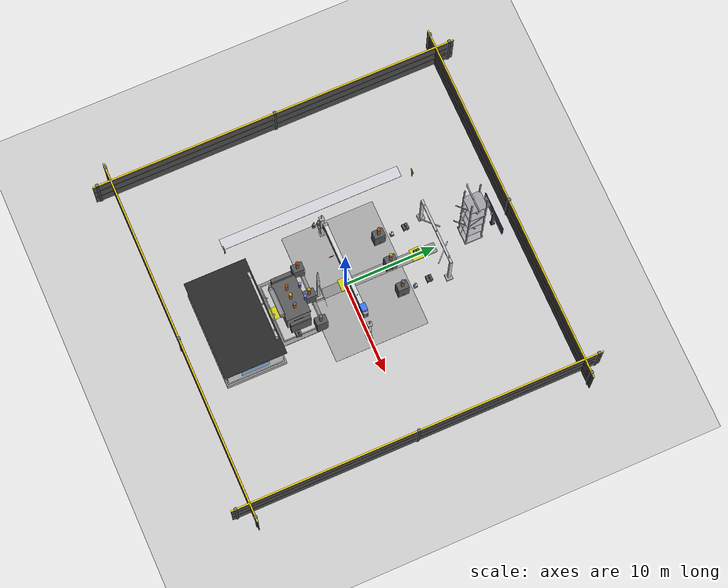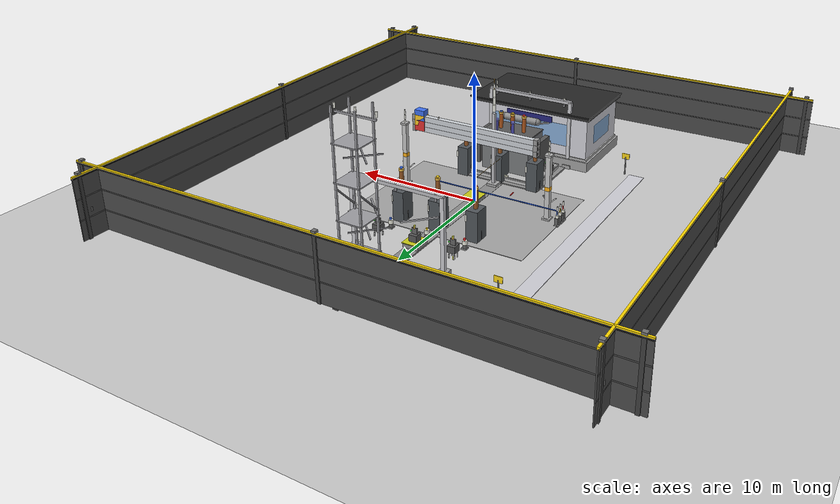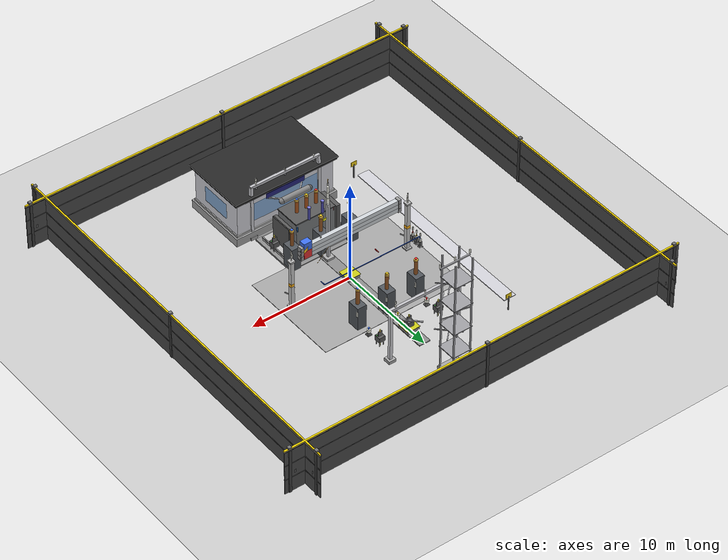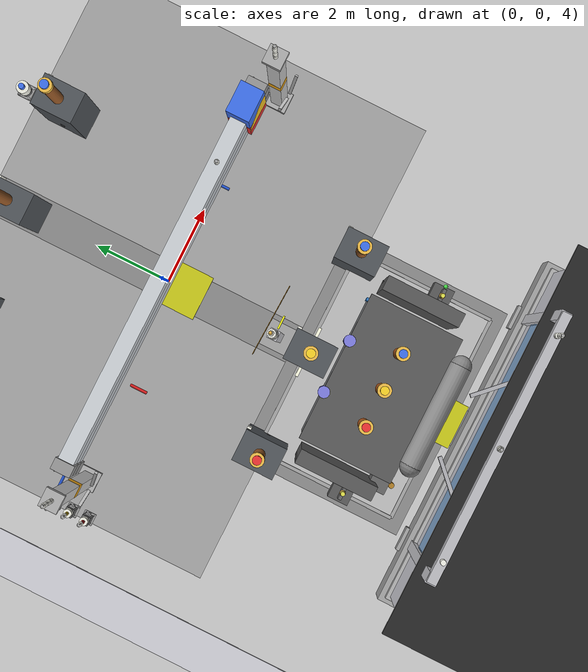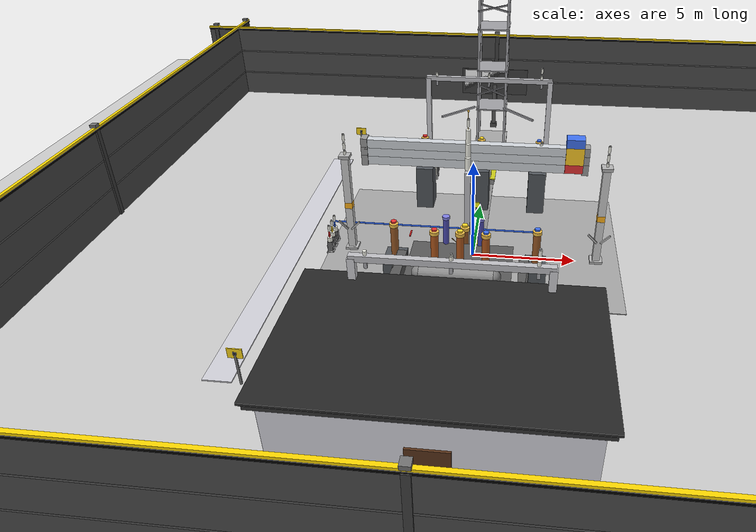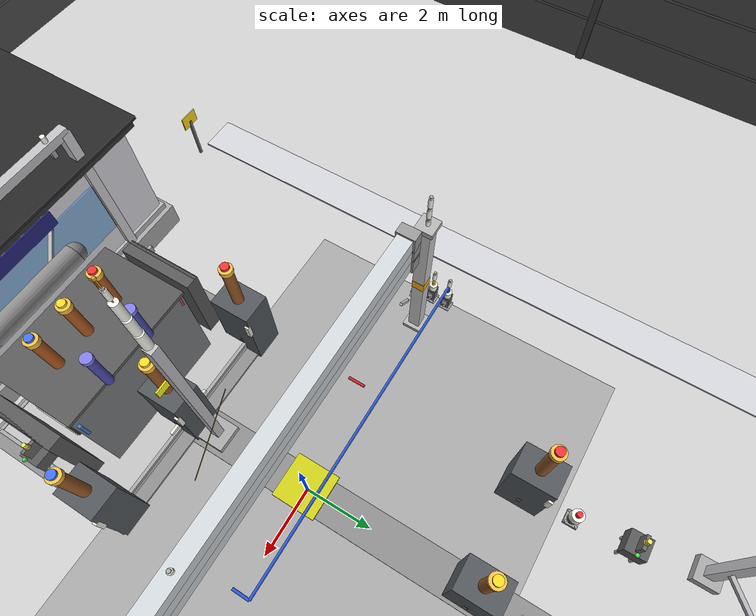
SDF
<sdf version="1.10">
 <world name="substation">
  <include><uri>model://ground</uri><name>ground</name></include>
  <include>
   <uri>model://yard_gravel_pad</uri>
   <name>yard_equipment_pad</name>
   <pose>0.000 1.000 0.000 0 0 0.00000</pose>
  </include>
  <include>
   <uri>model://oil_containment</uri>
   <name>oil_containment_zone</name>
   <pose>0.000 -6.000 0.000 0 0 0.00000</pose>
  </include>
  <include>
   <uri>model://walkway</uri>
   <name>walkway_main</name>
   <pose>-9.000 0.000 0.000 0 0 0.00000</pose>
  </include>
  <include><uri>model://cable_trench</uri><name>cable_trench_main</name></include>
  <include><uri>model://fence</uri><name>fence_north</name><pose>0.000 18.000 1.250 0 0 0.00000</pose></include>
  <include>
   <uri>model://fence</uri>
   <name>fence_south</name>
   <pose>0.000 -18.000 1.250 0 0 0.00000</pose>
  </include>
  <include><uri>model://fence</uri><name>fence_east</name><pose>18.000 0.000 1.250 0 0 1.57080</pose></include>
  <include><uri>model://fence</uri><name>fence_west</name><pose>-18.000 0.000 1.250 0 0 1.57080</pose></include>
  <include>
   <uri>model://name_board</uri>
   <name>substation_name_board</name>
   <pose>0.000 16.500 0.000 0 0 0.00000</pose>
  </include>
  <include>
   <uri>model://warning_sign</uri>
   <name>warning_sign_incoming</name>
   <pose>-8.000 11.000 0.000 0 0 0.00000</pose>
  </include>
  <include>
   <uri>model://warning_sign</uri>
   <name>warning_sign_outgoing</name>
   <pose>-8.000 -10.000 0.000 0 0 0.00000</pose>
  </include>
  <include>
   <uri>model://tower</uri>
   <name>tower_incoming</name>
   <pose>0.000 14.000 0.000 0 0 0.00000</pose>
  </include>
  <include>
   <uri>model://gantry</uri>
   <name>gantry_incoming</name>
   <pose>0.000 10.000 0.000 0 0 0.00000</pose>
  </include>
  <include>
   <uri>model://disconnector</uri>
   <name>disconnector_in_a</name>
   <pose>-3.000 8.000 0.000 0 0 0.00000</pose>
  </include>
  <include>
   <uri>model://ct_transformer_a</uri>
   <name>ct_a</name>
   <pose>-3.000 6.500 0.000 0 0 0.00000</pose>
  </include>
  <include>
   <uri>model://breaker_single_a</uri>
   <name>breaker_left</name>
   <pose>-3.000 5.000 0.000 0 0 0.00000</pose>
  </include>
  <include>
   <uri>model://disconnector</uri>
   <name>disconnector_in_b</name>
   <pose>0.000 8.000 0.000 0 0 0.00000</pose>
  </include>
  <include>
   <uri>model://ct_transformer_b</uri>
   <name>ct_b</name>
   <pose>0.000 6.500 0.000 0 0 0.00000</pose>
  </include>
  <include>
   <uri>model://breaker_single_b</uri>
   <name>breaker_center</name>
   <pose>0.000 5.000 0.000 0 0 0.00000</pose>
  </include>
  <include>
   <uri>model://disconnector</uri>
   <name>disconnector_in_c</name>
   <pose>3.000 8.000 0.000 0 0 0.00000</pose>
  </include>
  <include>
   <uri>model://ct_transformer_c</uri>
   <name>ct_c</name>
   <pose>3.000 6.500 0.000 0 0 0.00000</pose>
  </include>
  <include>
   <uri>model://breaker_single_c</uri>
   <name>breaker_right</name>
   <pose>3.000 5.000 0.000 0 0 0.00000</pose>
  </include>
  <include>
   <uri>model://busbar_support</uri>
   <name>busbar_support_west</name>
   <pose>-6.000 0.000 0.000 0 0 0.00000</pose>
  </include>
  <include>
   <uri>model://busbar_support</uri>
   <name>busbar_support_east</name>
   <pose>6.000 0.000 0.000 0 0 0.00000</pose>
  </include>
  <include>
   <uri>model://insulator</uri>
   <name>ins_busbar_w_a</name>
   <pose>-6.000 0.000 5.000 0 0 0</pose>
  </include>
  <include>
   <uri>model://insulator</uri>
   <name>ins_busbar_w_b</name>
   <pose>-6.000 0.000 5.400 0 0 0</pose>
  </include>
  <include>
   <uri>model://insulator</uri>
   <name>ins_busbar_w_c</name>
   <pose>-6.000 0.000 5.800 0 0 0</pose>
  </include>
  <include><uri>model://insulator</uri><name>ins_busbar_e_a</name><pose>6.000 0.000 5.000 0 0 0</pose></include>
  <include><uri>model://insulator</uri><name>ins_busbar_e_b</name><pose>6.000 0.000 5.400 0 0 0</pose></include>
  <include><uri>model://insulator</uri><name>ins_busbar_e_c</name><pose>6.000 0.000 5.800 0 0 0</pose></include>
  <include><uri>model://busbar_a</uri><name>busbar_a</name><pose>0.000 0.000 5.000 0 0 0.00000</pose></include>
  <include><uri>model://busbar_b</uri><name>busbar_b</name><pose>0.000 0.000 5.400 0 0 0.00000</pose></include>
  <include><uri>model://busbar_c</uri><name>busbar_c</name><pose>0.000 0.000 5.800 0 0 0.00000</pose></include>
  <include>
   <uri>model://pt_transformer_a</uri>
   <name>pt_a</name>
   <pose>-7.000 -0.500 0.000 0 0 0.00000</pose>
  </include>
  <include>
   <uri>model://pt_transformer_b</uri>
   <name>pt_b</name>
   <pose>-7.000 0.000 0.000 0 0 0.00000</pose>
  </include>
  <include>
   <uri>model://pt_transformer_c</uri>
   <name>pt_c</name>
   <pose>-7.000 0.500 0.000 0 0 0.00000</pose>
  </include>
  <include>
   <uri>model://transformer_pad</uri>
   <name>transformer_pad_main</name>
   <pose>0.000 -6.000 0.000 0 0 0.00000</pose>
  </include>
  <include>
   <uri>model://transformer</uri>
   <name>transformer_main</name>
   <pose>0.000 -6.000 0.500 0 0 0.00000</pose>
  </include>
  <include>
   <uri>model://lightning_arrester</uri>
   <name>arrester_surge_protection</name>
   <pose>0.000 -3.000 0.000 0 0 0.00000</pose>
  </include>
  <include>
   <uri>model://insulator</uri>
   <name>ins_arrester_top</name>
   <pose>0.000 -3.000 8.000 0 0 0</pose>
  </include>
  <include>
   <uri>model://gantry</uri>
   <name>gantry_outgoing</name>
   <pose>0.000 -9.000 0.000 0 0 0.00000</pose>
  </include>
  <include>
   <uri>model://disconnector</uri>
   <name>disconnector_out_a</name>
   <pose>-3.000 -6.500 0.000 0 0 0.00000</pose>
  </include>
  <include>
   <uri>model://breaker_single_a</uri>
   <name>breaker_out_a</name>
   <pose>-3.000 -4.000 0.000 0 0 0.00000</pose>
  </include>
  <include>
   <uri>model://disconnector</uri>
   <name>disconnector_out_b</name>
   <pose>0.000 -6.500 0.000 0 0 0.00000</pose>
  </include>
  <include>
   <uri>model://breaker_single_b</uri>
   <name>breaker_out_b</name>
   <pose>0.000 -4.000 0.000 0 0 0.00000</pose>
  </include>
  <include>
   <uri>model://disconnector</uri>
   <name>disconnector_out_c</name>
   <pose>3.000 -6.500 0.000 0 0 0.00000</pose>
  </include>
  <include>
   <uri>model://breaker_single_c</uri>
   <name>breaker_out_c</name>
   <pose>3.000 -4.000 0.000 0 0 0.00000</pose>
  </include>
  <include>
   <uri>model://control_room</uri>
   <name>control_room_main</name>
   <pose>0.000 -12.000 0.800 0 0 0.00000</pose>
  </include>
  <include><uri>model://insulator</uri><name>ins_A_gantry</name><pose>-3.000 10.000 5.150 0 0 0</pose></include>
  <include><uri>model://insulator</uri><name>ins_A_busbar</name><pose>-3.000 0.000 5.000 0 0 0</pose></include>
  <include><uri>model://insulator</uri><name>ins_B_gantry</name><pose>0.000 10.000 5.550 0 0 0</pose></include>
  <include><uri>model://insulator</uri><name>ins_B_busbar</name><pose>0.000 0.000 5.400 0 0 0</pose></include>
  <include><uri>model://insulator</uri><name>ins_C_gantry</name><pose>3.000 10.000 5.950 0 0 0</pose></include>
  <include><uri>model://insulator</uri><name>ins_C_busbar</name><pose>3.000 0.000 5.800 0 0 0</pose></include>
  <include><uri>model://insulator</uri><name>ins_A_pt_bus</name><pose>-3.000 0.000 5.000 0 0 0</pose></include>
  <include>
   <uri>model://wire_0p5m_red</uri>
   <name>A_pt_lane</name>
   <pose>-3.000 -0.250 1.200 1.57080 0.00000 0.00000</pose>
  </include>
  <include><uri>model://insulator</uri><name>ins_A_pt</name><pose>-7.000 -0.500 1.200 0 0 0</pose></include>
  <include>
   <uri>model://wire_0p5m_red</uri>
   <name>A_pt_drop2</name>
   <pose>-7.000 -0.500 0.950 0.00000 0.00000 0.00000</pose>
  </include>
  <include><uri>model://insulator</uri><name>ins_B_pt_bus</name><pose>0.000 0.000 5.400 0 0 0</pose></include>
  <include><uri>model://insulator</uri><name>ins_B_pt</name><pose>-7.000 0.000 1.200 0 0 0</pose></include>
  <include>
   <uri>model://wire_0p5m_yellow</uri>
   <name>B_pt_drop2</name>
   <pose>-7.000 0.000 0.950 0.00000 0.00000 0.00000</pose>
  </include>
  <include><uri>model://insulator</uri><name>ins_C_pt_bus</name><pose>3.000 0.000 5.800 0 0 0</pose></include>
  <include>
   <uri>model://wire_0p5m_blue</uri>
   <name>C_pt_lane</name>
   <pose>3.000 0.250 1.200 1.57080 0.00000 0.00000</pose>
  </include>
  <include>
   <uri>model://wire_10p0m_blue</uri>
   <name>C_pt_west</name>
   <pose>-2.000 0.500 1.200 0.00000 1.57080 0.00000</pose>
  </include>
  <include><uri>model://insulator</uri><name>ins_C_pt</name><pose>-7.000 0.500 1.200 0 0 0</pose></include>
  <include>
   <uri>model://wire_0p5m_blue</uri>
   <name>C_pt_drop2</name>
   <pose>-7.000 0.500 0.950 0.00000 0.00000 0.00000</pose>
  </include>
  <include><uri>model://insulator</uri><name>ins_A_xfmr</name><pose>-1.000 -6.000 4.500 0 0 0</pose></include>
  <include>
   <uri>model://wire_0p5m_red</uri>
   <name>A_xfmr_drop</name>
   <pose>-1.000 -6.000 4.750 0.00000 0.00000 0.00000</pose>
  </include>
  <include><uri>model://insulator</uri><name>ins_B_xfmr</name><pose>0.000 -6.000 4.500 0 0 0</pose></include>
  <include><uri>model://insulator</uri><name>ins_C_xfmr</name><pose>1.000 -6.000 4.500 0 0 0</pose></include>
  <include>
   <uri>model://insulator</uri>
   <name>ins_A_out_gantry</name>
   <pose>-3.000 -9.000 5.150 0 0 0</pose>
  </include>
  <include>
   <uri>model://insulator</uri>
   <name>ins_B_out_gantry</name>
   <pose>0.000 -9.000 5.550 0 0 0</pose>
  </include>
  <include>
   <uri>model://insulator</uri>
   <name>ins_C_out_gantry</name>
   <pose>3.000 -9.000 5.950 0 0 0</pose>
  </include>
  <light name="sun" type="directional">
   <pose>0 0 50 0 0 0</pose>
   <diffuse>1 1 1 1</diffuse>
   <specular>0.4 0.4 0.4 1</specular>
   <direction>-0.5 -0.4 -1</direction>
  </light>
 </world>
</sdf>

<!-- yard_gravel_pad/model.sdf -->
<sdf version="1.10">
  <model name="yard_gravel_pad">
    <static>true</static>
    <link name="link">
      <visual name="gravel_surface">
        <pose>0 0 0.02 0 0 0</pose>
        <geometry>
          <box>
            <size>14 10 0.04</size>
          </box>
        </geometry>
        <material>
          <script>
            <uri>model://ground/materials/scripts</uri>
            <uri>model://ground/materials/textures</uri>
            <name>Gazebo/Gravel</name>
          </script>
        </material>
      </visual>
      <visual name="concrete_curb">
        <pose>0 0 0.06 0 0 0</pose>
        <geometry>
          <box>
            <size>14.2 10.2 0.04</size>
          </box>
        </geometry>
        <material>
          <ambient>0.55 0.55 0.55 1</ambient>
          <diffuse>0.65 0.65 0.65 1</diffuse>
        </material>
      </visual>
    </link>
  </model>
</sdf>

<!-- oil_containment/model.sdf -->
<sdf version="1.10">
  <model name="oil_containment">
    <static>true</static>
    <link name="link">
      <visual name="berm">
        <pose>0 0 0.08 0 0 0</pose>
        <geometry>
          <box>
            <size>7 5 0.16</size>
          </box>
        </geometry>
        <material>
          <ambient>0.45 0.45 0.45 1</ambient>
          <diffuse>0.55 0.55 0.55 1</diffuse>
        </material>
      </visual>
      <visual name="inner">
        <pose>0 0 0.04 0 0 0</pose>
        <geometry>
          <box>
            <size>6.4 4.4 0.08</size>
          </box>
        </geometry>
        <material>
          <ambient>0.35 0.35 0.35 1</ambient>
          <diffuse>0.42 0.42 0.42 1</diffuse>
        </material>
      </visual>
    </link>
  </model>
</sdf>

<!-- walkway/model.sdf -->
<sdf version="1.10">
  <model name="walkway">
    <static>true</static>
    <link name="link">
      <visual name="path">
        <pose>0 0 0.03 0 0 0</pose>
        <geometry>
          <box>
            <size>1.2 20 0.06</size>
          </box>
        </geometry>
        <material>
          <ambient>0.7 0.7 0.72 1</ambient>
          <diffuse>0.82 0.82 0.85 1</diffuse>
        </material>
      </visual>
    </link>
  </model>
</sdf>

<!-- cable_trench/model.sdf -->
<sdf version="1.10">

<model name="cable_trench">

  <static>true</static>

  <link name="link">

    <!-- CONCRETE TRENCH BODY -->
    <visual name="trench_main">
      <pose>0 0 -0.25 0 0 0</pose>
      <geometry>
        <box>
          <size>1.0 20.0 0.5</size>
        </box>
      </geometry>
      <material>
        <ambient>0.6 0.6 0.6 1</ambient>
        <diffuse>0.65 0.65 0.65 1</diffuse>
        <specular>0.1 0.1 0.1 1</specular>
      </material>
    </visual>

    <!-- CABLE DUCT LINERS -->
    <visual name="duct_left">
      <pose>-0.2 0 -0.25 0 0 0</pose>
      <geometry>
        <box>
          <size>0.18 20.0 0.15</size>
        </box>
      </geometry>
      <material>
        <ambient>0.4 0.4 0.4 1</ambient>
        <diffuse>0.45 0.45 0.45 1</diffuse>
      </material>
    </visual>

    <visual name="duct_center">
      <pose>0 0 -0.25 0 0 0</pose>
      <geometry>
        <box>
          <size>0.18 20.0 0.15</size>
        </box>
      </geometry>
      <material>
        <ambient>0.4 0.4 0.4 1</ambient>
        <diffuse>0.45 0.45 0.45 1</diffuse>
      </material>
    </visual>

    <visual name="duct_right">
      <pose>0.2 0 -0.25 0 0 0</pose>
      <geometry>
        <box>
          <size>0.18 20.0 0.15</size>
        </box>
      </geometry>
      <material>
        <ambient>0.4 0.4 0.4 1</ambient>
        <diffuse>0.45 0.45 0.45 1</diffuse>
      </material>
    </visual>

    <!-- TRENCH COVER (GRATE) -->
    <visual name="cover_main">
      <pose>0 0 0.05 0 0 0</pose>
      <geometry>
        <box>
          <size>1.1 20.2 0.1</size>
        </box>
      </geometry>
      <material>
        <ambient>0.5 0.5 0.5 1</ambient>
        <diffuse>0.55 0.55 0.55 1</diffuse>
      </material>
    </visual>

    <!-- GRATING PATTERN -->
    <visual name="grate_line_1">
      <pose>-0.3 0 0.06 0 0 0</pose>
      <geometry>
        <box>
          <size>0.05 20.0 0.05</size>
        </box>
      </geometry>
      <material>
        <ambient>0.4 0.4 0.4 1</ambient>
        <diffuse>0.45 0.45 0.45 1</diffuse>
      </material>
    </visual>

    <visual name="grate_line_2">
      <pose>0 0 0.06 0 0 0</pose>
      <geometry>
        <box>
          <size>0.05 20.0 0.05</size>
        </box>
      </geometry>
      <material>
        <ambient>0.4 0.4 0.4 1</ambient>
        <diffuse>0.45 0.45 0.45 1</diffuse>
      </material>
    </visual>

    <visual name="grate_line_3">
      <pose>0.3 0 0.06 0 0 0</pose>
      <geometry>
        <box>
          <size>0.05 20.0 0.05</size>
        </box>
      </geometry>
      <material>
        <ambient>0.4 0.4 0.4 1</ambient>
        <diffuse>0.45 0.45 0.45 1</diffuse>
      </material>
    </visual>

    <!-- ACCESS JUNCTION BOX 1 -->
    <visual name="junction_1_body">
      <pose>0 -8 0.3 0 0 0</pose>
      <geometry>
        <box>
          <size>1.2 1.2 0.3</size>
        </box>
      </geometry>
      <material>
        <ambient>0.5 0.5 0.5 1</ambient>
        <diffuse>0.55 0.55 0.55 1</diffuse>
      </material>
    </visual>

    <visual name="junction_1_cover">
      <pose>0 -8 0.5 0 0 0</pose>
      <geometry>
        <box>
          <size>1.3 1.3 0.05</size>
        </box>
      </geometry>
      <material>
        <ambient>0.7 0.7 0 1</ambient>
        <diffuse>0.8 0.8 0.1 1</diffuse>
      </material>
    </visual>

    <!-- ACCESS JUNCTION BOX 2 -->
    <visual name="junction_2_body">
      <pose>0 0 0.3 0 0 0</pose>
      <geometry>
        <box>
          <size>1.2 1.2 0.3</size>
        </box>
      </geometry>
      <material>
        <ambient>0.5 0.5 0.5 1</ambient>
        <diffuse>0.55 0.55 0.55 1</diffuse>
      </material>
    </visual>

    <visual name="junction_2_cover">
      <pose>0 0 0.5 0 0 0</pose>
      <geometry>
        <box>
          <size>1.3 1.3 0.05</size>
        </box>
      </geometry>
      <material>
        <ambient>0.7 0.7 0 1</ambient>
        <diffuse>0.8 0.8 0.1 1</diffuse>
      </material>
    </visual>

    <!-- ACCESS JUNCTION BOX 3 -->
    <visual name="junction_3_body">
      <pose>0 8 0.3 0 0 0</pose>
      <geometry>
        <box>
          <size>1.2 1.2 0.3</size>
        </box>
      </geometry>
      <material>
        <ambient>0.5 0.5 0.5 1</ambient>
        <diffuse>0.55 0.55 0.55 1</diffuse>
      </material>
    </visual>

    <visual name="junction_3_cover">
      <pose>0 8 0.5 0 0 0</pose>
      <geometry>
        <box>
          <size>1.3 1.3 0.05</size>
        </box>
      </geometry>
      <material>
        <ambient>0.7 0.7 0 1</ambient>
        <diffuse>0.8 0.8 0.1 1</diffuse>
      </material>
    </visual>

    <!-- COLLISION -->
    <collision name="trench_collision">
      <pose>0 0 -0.25 0 0 0</pose>
      <geometry>
        <box>
          <size>1.0 20.0 0.5</size>
        </box>
      </geometry>
    </collision>

    <collision name="cover_collision">
      <pose>0 0 0.05 0 0 0</pose>
      <geometry>
        <box>
          <size>1.1 20.2 0.1</size>
        </box>
      </geometry>
    </collision>

  </link>

</model>

</sdf>

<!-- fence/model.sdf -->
<sdf version="1.10">

  <model name="fence">

    <static>true</static>

    <link name="link">

      <!-- MAIN SECURITY FENCE PANEL -->

      <visual name="fence_panel_mesh">
        <pose>0 0 2.25 0 0 0</pose>
        <geometry>
          <box>
            <size>40 0.08 4.5</size>
          </box>
        </geometry>
        <material>
          <ambient>0.2 0.2 0.2 1</ambient>
          <diffuse>0.3 0.3 0.3 1</diffuse>
          <specular>0.15 0.15 0.15 1</specular>
        </material>
      </visual>

      <!-- Fence grid pattern (visual effect) -->
      <visual name="fence_horizontal_grid_1">
        <pose>0 0 1.5 0 0 0</pose>
        <geometry>
          <box>
            <size>40 0.1 0.08</size>
          </box>
        </geometry>
        <material>
          <ambient>0.25 0.25 0.25 1</ambient>
          <diffuse>0.35 0.35 0.35 1</diffuse>
        </material>
      </visual>

      <visual name="fence_horizontal_grid_2">
        <pose>0 0 3.0 0 0 0</pose>
        <geometry>
          <box>
            <size>40 0.1 0.08</size>
          </box>
        </geometry>
        <material>
          <ambient>0.25 0.25 0.25 1</ambient>
          <diffuse>0.35 0.35 0.35 1</diffuse>
        </material>
      </visual>

      <!-- TOP SAFETY STRIPE -->

      <visual name="warning_strip_yellow">
        <pose>0 0 4.55 0 0 0</pose>
        <geometry>
          <box>
            <size>40 0.15 0.2</size>
          </box>
        </geometry>
        <material>
          <ambient>1 0.85 0 1</ambient>
          <diffuse>1 0.85 0 1</diffuse>
        </material>
      </visual>

      <visual name="warning_strip_text">
        <pose>0 0 4.5 0 0 0</pose>
        <geometry>
          <box>
            <size>40 0.18 0.1</size>
          </box>
        </geometry>
        <material>
          <ambient>0 0 0 1</ambient>
          <diffuse>0 0 0 1</diffuse>
        </material>
      </visual>

      <!-- REINFORCED CORNER POSTS -->

      <visual name="post_left">
        <pose>-19.5 0 2.25 0 0 0</pose>
        <geometry>
          <box>
            <size>0.25 0.25 4.5</size>
          </box>
        </geometry>
        <material>
          <ambient>0.15 0.15 0.15 1</ambient>
          <diffuse>0.25 0.25 0.25 1</diffuse>
        </material>
      </visual>

      <!-- Post top cap -->
      <visual name="post_left_cap">
        <pose>-19.5 0 4.75 0 0 0</pose>
        <geometry>
          <box>
            <size>0.3 0.3 0.15</size>
          </box>
        </geometry>
        <material>
          <ambient>0.35 0.35 0.35 1</ambient>
          <diffuse>0.45 0.45 0.45 1</diffuse>
        </material>
      </visual>

      <visual name="post_center">
        <pose>0 0 2.25 0 0 0</pose>
        <geometry>
          <box>
            <size>0.25 0.25 4.5</size>
          </box>
        </geometry>
        <material>
          <ambient>0.15 0.15 0.15 1</ambient>
          <diffuse>0.25 0.25 0.25 1</diffuse>
        </material>
      </visual>

      <visual name="post_center_cap">
        <pose>0 0 4.75 0 0 0</pose>
        <geometry>
          <box>
            <size>0.3 0.3 0.15</size>
          </box>
        </geometry>
        <material>
          <ambient>0.35 0.35 0.35 1</ambient>
          <diffuse>0.45 0.45 0.45 1</diffuse>
        </material>
      </visual>

      <visual name="post_right">
        <pose>19.5 0 2.25 0 0 0</pose>
        <geometry>
          <box>
            <size>0.25 0.25 4.5</size>
          </box>
        </geometry>
        <material>
          <ambient>0.15 0.15 0.15 1</ambient>
          <diffuse>0.25 0.25 0.25 1</diffuse>
        </material>
      </visual>

      <visual name="post_right_cap">
        <pose>19.5 0 4.75 0 0 0</pose>
        <geometry>
          <box>
            <size>0.3 0.3 0.15</size>
          </box>
        </geometry>
        <material>
          <ambient>0.35 0.35 0.35 1</ambient>
          <diffuse>0.45 0.45 0.45 1</diffuse>
        </material>
      </visual>

      <!-- GATE HINGE AREA -->
      <visual name="gate_hinge">
        <pose>19 0 2.0 0 0 0</pose>
        <geometry>
          <cylinder>
            <radius>0.08</radius>
            <length>0.3</length>
          </cylinder>
        </geometry>
        <material>
          <ambient>0.3 0.3 0.3 1</ambient>
          <diffuse>0.4 0.4 0.4 1</diffuse>
        </material>
      </visual>

      <!-- COLLISION -->

    </link>
  </model>
</sdf>

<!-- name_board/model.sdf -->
<sdf version="1.10">

<model name="name_board">

  <static>true</static>

  <link name="board">

    <!-- MAIN SUPPORT POLE -->
    <visual name="pole_main">
      <pose>0 0 1.5 0 0 0</pose>
      <geometry>
        <box>
          <size>0.25 0.25 3</size>
        </box>
      </geometry>
      <material>
        <ambient>0.25 0.25 0.25 1</ambient>
        <diffuse>0.35 0.35 0.35 1</diffuse>
        <specular>0.1 0.1 0.1 1</specular>
      </material>
    </visual>

    <!-- Pole base foot -->
    <visual name="pole_base">
      <pose>0 0 0.15 0 0 0</pose>
      <geometry>
        <box>
          <size>0.4 0.4 0.3</size>
        </box>
      </geometry>
      <material>
        <ambient>0.2 0.2 0.2 1</ambient>
        <diffuse>0.3 0.3 0.3 1</diffuse>
      </material>
    </visual>

    <!-- INFORMATION SIGN BOARD -->
    <visual name="sign_main">
      <pose>0 0 3.2 0 0 0</pose>
      <geometry>
        <box>
          <size>4.2 0.08 1.6</size>
        </box>
      </geometry>
      <material>
        <ambient>0 0 0.5 1</ambient>
        <diffuse>0 0 0.6 1</diffuse>
        <specular>0.3 0.3 0.3 1</specular>
      </material>
    </visual>

    <!-- White text area background -->
    <visual name="sign_text_area">
      <pose>0 -0.04 3.2 0 0 0</pose>
      <geometry>
        <box>
          <size>4 0.05 1.5</size>
        </box>
      </geometry>
      <material>
        <ambient>0.95 0.95 0.95 1</ambient>
        <diffuse>1 1 1 1</diffuse>
      </material>
    </visual>

    <!-- Sign border frame -->
    <visual name="sign_border">
      <pose>0 -0.05 3.2 0 0 0</pose>
      <geometry>
        <box>
          <size>4.3 0.03 1.7</size>
        </box>
      </geometry>
      <material>
        <ambient>0.15 0.15 0.15 1</ambient>
        <diffuse>0.25 0.25 0.25 1</diffuse>
      </material>
    </visual>

    <!-- LIGHT FIXTURE (NIGHT ILLUMINATION) -->
    <visual name="light_fixture">
      <pose>0 -0.25 3.5 0 0 0</pose>
      <geometry>
        <box>
          <size>0.3 0.15 0.15</size>
        </box>
      </geometry>
      <material>
        <ambient>0.3 0.3 0.3 1</ambient>
        <diffuse>0.4 0.4 0.4 1</diffuse>
      </material>
    </visual>

    <visual name="light_bulb">
      <pose>0 -0.32 3.5 0 0 0</pose>
      <geometry>
        <sphere>
          <radius>0.08</radius>
        </sphere>
      </geometry>
      <material>
        <ambient>1 1 0.8 1</ambient>
        <diffuse>1 1 0.9 1</diffuse>
        <emissive>0.8 0.8 0.6 0.5</emissive>
      </material>
    </visual>

  </link>

</model>

</sdf>

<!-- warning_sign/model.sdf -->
<sdf version="1.10">
  <model name="warning_sign">
    <static>true</static>
    <link name="link">
      <visual name="post">
        <pose>0 0 0.75 0 0 0</pose>
        <geometry>
          <box>
            <size>0.08 0.08 1.5</size>
          </box>
        </geometry>
        <material>
          <ambient>0.4 0.4 0.4 1</ambient>
          <diffuse>0.5 0.5 0.5 1</diffuse>
        </material>
      </visual>
      <visual name="sign">
        <pose>0 0 1.55 0 0 0</pose>
        <geometry>
          <box>
            <size>0.6 0.04 0.45</size>
          </box>
        </geometry>
        <material>
          <ambient>0.9 0.75 0.05 1</ambient>
          <diffuse>1 0.85 0.1 1</diffuse>
        </material>
      </visual>
      <visual name="symbol">
        <pose>0 -0.025 1.55 0 0 0</pose>
        <geometry>
          <box>
            <size>0.15 0.02 0.15</size>
          </box>
        </geometry>
        <material>
          <ambient>0.1 0.1 0.1 1</ambient>
          <diffuse>0.15 0.15 0.15 1</diffuse>
        </material>
      </visual>
    </link>
  </model>
</sdf>

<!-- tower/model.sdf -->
<sdf version="1.10">
  <model name="tower">
    <static>true</static>
    <link name="link">

      <!-- 2m x 2m concrete foundation -->
      <visual name="foundation">
        <pose>0 0 0.15 0 0 0</pose>
        <geometry>
          <box><size>2.0 2.0 0.3</size></box>
        </geometry>
        <material>
          <ambient>0.55 0.55 0.55 1</ambient>
          <diffuse>0.65 0.65 0.65 1</diffuse>
        </material>
      </visual>

      <!-- Four lattice legs (12 m) -->
      <visual name="leg_fl">
        <pose>-0.85 -0.85 6.15 0 0 0</pose>
        <geometry><box><size>0.12 0.12 12.3</size></box></geometry>
        <material><ambient>0.58 0.58 0.60 1</ambient><diffuse>0.68 0.68 0.70 1</diffuse></material>
      </visual>
      <visual name="leg_fr">
        <pose>0.85 -0.85 6.15 0 0 0</pose>
        <geometry><box><size>0.12 0.12 12.3</size></box></geometry>
        <material><ambient>0.58 0.58 0.60 1</ambient><diffuse>0.68 0.68 0.70 1</diffuse></material>
      </visual>
      <visual name="leg_bl">
        <pose>-0.85 0.85 6.15 0 0 0</pose>
        <geometry><box><size>0.12 0.12 12.3</size></box></geometry>
        <material><ambient>0.58 0.58 0.60 1</ambient><diffuse>0.68 0.68 0.70 1</diffuse></material>
      </visual>
      <visual name="leg_br">
        <pose>0.85 0.85 6.15 0 0 0</pose>
        <geometry><box><size>0.12 0.12 12.3</size></box></geometry>
        <material><ambient>0.58 0.58 0.60 1</ambient><diffuse>0.68 0.68 0.70 1</diffuse></material>
      </visual>

      <!-- Horizontal lattice belts -->
      <visual name="belt_1"><pose>0 0 2.5 0 0 0</pose><geometry><box><size>1.9 1.9 0.08</size></box></geometry>
        <material><ambient>0.52 0.52 0.54 1</ambient><diffuse>0.62 0.62 0.64 1</diffuse></material></visual>
      <visual name="belt_2"><pose>0 0 5.0 0 0 0</pose><geometry><box><size>1.9 1.9 0.08</size></box></geometry>
        <material><ambient>0.52 0.52 0.54 1</ambient><diffuse>0.62 0.62 0.64 1</diffuse></material></visual>
      <visual name="belt_3"><pose>0 0 7.5 0 0 0</pose><geometry><box><size>1.9 1.9 0.08</size></box></geometry>
        <material><ambient>0.52 0.52 0.54 1</ambient><diffuse>0.62 0.62 0.64 1</diffuse></material></visual>
      <visual name="belt_4"><pose>0 0 10.0 0 0 0</pose><geometry><box><size>1.9 1.9 0.08</size></box></geometry>
        <material><ambient>0.52 0.52 0.54 1</ambient><diffuse>0.62 0.62 0.64 1</diffuse></material></visual>

      <!-- Diagonal bracing (X pattern on front face) -->
      <visual name="diag_f1"><pose>0 -0.85 3.75 0 0 0.785</pose><geometry><box><size>2.4 0.08 0.08</size></box></geometry>
        <material><ambient>0.50 0.50 0.52 1</ambient><diffuse>0.60 0.60 0.62 1</diffuse></material></visual>
      <visual name="diag_f2"><pose>0 -0.85 3.75 0 0 -0.785</pose><geometry><box><size>2.4 0.08 0.08</size></box></geometry>
        <material><ambient>0.50 0.50 0.52 1</ambient><diffuse>0.60 0.60 0.62 1</diffuse></material></visual>
      <visual name="diag_f3"><pose>0 -0.85 8.75 0 0 0.785</pose><geometry><box><size>2.4 0.08 0.08</size></box></geometry>
        <material><ambient>0.50 0.50 0.52 1</ambient><diffuse>0.60 0.60 0.62 1</diffuse></material></visual>
      <visual name="diag_f4"><pose>0 -0.85 8.75 0 0 -0.785</pose><geometry><box><size>2.4 0.08 0.08</size></box></geometry>
        <material><ambient>0.50 0.50 0.52 1</ambient><diffuse>0.60 0.60 0.62 1</diffuse></material></visual>

      <!-- Side bracing -->
      <visual name="diag_s1"><pose>0.85 0 6.25 0.785 0 0</pose><geometry><box><size>0.08 2.4 0.08</size></box></geometry>
        <material><ambient>0.50 0.50 0.52 1</ambient><diffuse>0.60 0.60 0.62 1</diffuse></material></visual>
      <visual name="diag_s2"><pose>-0.85 0 6.25 0.785 0 0</pose><geometry><box><size>0.08 2.4 0.08</size></box></geometry>
        <material><ambient>0.50 0.50 0.52 1</ambient><diffuse>0.60 0.60 0.62 1</diffuse></material></visual>

      <!-- Top crossarm (3 m) -->
      <visual name="crossarm">
        <pose>0 -0.3 11.5 0 0 0</pose>
        <geometry><box><size>3.0 0.12 0.12</size></box></geometry>
        <material><ambient>0.55 0.55 0.57 1</ambient><diffuse>0.65 0.65 0.67 1</diffuse></material>
      </visual>

      <!-- Climbing rungs -->
      <visual name="rung_1"><pose>-0.85 -0.85 4.0 0 0 0.785</pose><geometry><cylinder><radius>0.02</radius><length>0.9</length></cylinder></geometry>
        <material><ambient>0.45 0.45 0.45 1</ambient><diffuse>0.55 0.55 0.55 1</diffuse></material></visual>
      <visual name="rung_2"><pose>-0.85 -0.85 7.0 0 0 0.785</pose><geometry><cylinder><radius>0.02</radius><length>0.9</length></cylinder></geometry>
        <material><ambient>0.45 0.45 0.45 1</ambient><diffuse>0.55 0.55 0.55 1</diffuse></material></visual>
      <visual name="rung_3"><pose>-0.85 -0.85 10.0 0 0 0.785</pose><geometry><cylinder><radius>0.02</radius><length>0.9</length></cylinder></geometry>
        <material><ambient>0.45 0.45 0.45 1</ambient><diffuse>0.55 0.55 0.55 1</diffuse></material></visual>

      <!-- Phase A insulator (left) -->
      <visual name="ins_a">
        <pose>-1.5 -0.3 11.85 0 0 0</pose>
        <geometry><cylinder><radius>0.07</radius><length>0.35</length></cylinder></geometry>
        <material><ambient>0.92 0.92 0.88 1</ambient><diffuse>0.97 0.97 0.93 1</diffuse></material>
      </visual>
      <!-- Phase B insulator (center) -->
      <visual name="ins_b">
        <pose>0 -0.3 11.85 0 0 0</pose>
        <geometry><cylinder><radius>0.07</radius><length>0.35</length></cylinder></geometry>
        <material><ambient>0.92 0.92 0.88 1</ambient><diffuse>0.97 0.97 0.93 1</diffuse></material>
      </visual>
      <!-- Phase C insulator (right) -->
      <visual name="ins_c">
        <pose>1.5 -0.3 11.85 0 0 0</pose>
        <geometry><cylinder><radius>0.07</radius><length>0.35</length></cylinder></geometry>
        <material><ambient>0.92 0.92 0.88 1</ambient><diffuse>0.97 0.97 0.93 1</diffuse></material>
      </visual>

      <collision name="collision">
        <pose>0 0 6.15 0 0 0</pose>
        <geometry><box><size>2.0 2.0 12.3</size></box></geometry>
      </collision>
    </link>
  </model>
</sdf>

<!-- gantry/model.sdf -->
<sdf version="1.10">
  <model name="gantry">
    <static>true</static>
    <link name="link">

      <!-- Concrete footings -->
      <visual name="foot_l"><pose>-3.5 0 0.15 0 0 0</pose><geometry><box><size>0.7 0.7 0.3</size></box></geometry>
        <material><ambient>0.55 0.55 0.55 1</ambient><diffuse>0.65 0.65 0.65 1</diffuse></material></visual>
      <visual name="foot_r"><pose>3.5 0 0.15 0 0 0</pose><geometry><box><size>0.7 0.7 0.3</size></box></geometry>
        <material><ambient>0.55 0.55 0.55 1</ambient><diffuse>0.65 0.65 0.65 1</diffuse></material></visual>

      <!-- Vertical columns -->
      <visual name="col_l"><pose>-3.5 0 2.75 0 0 0</pose><geometry><box><size>0.28 0.28 5.5</size></box></geometry>
        <material><ambient>0.72 0.72 0.74 1</ambient><diffuse>0.82 0.82 0.84 1</diffuse></material></visual>
      <visual name="col_r"><pose>3.5 0 2.75 0 0 0</pose><geometry><box><size>0.28 0.28 5.5</size></box></geometry>
        <material><ambient>0.72 0.72 0.74 1</ambient><diffuse>0.82 0.82 0.84 1</diffuse></material></visual>

      <!-- Cross bracing -->
      <visual name="brace_l"><pose>-1.75 0 3.5 0 0 0.785</pose><geometry><box><size>2.5 0.1 0.1</size></box></geometry>
        <material><ambient>0.60 0.60 0.62 1</ambient><diffuse>0.70 0.70 0.72 1</diffuse></material></visual>
      <visual name="brace_r"><pose>1.75 0 3.5 0 0 -0.785</pose><geometry><box><size>2.5 0.1 0.1</size></box></geometry>
        <material><ambient>0.60 0.60 0.62 1</ambient><diffuse>0.70 0.70 0.72 1</diffuse></material></visual>

      <!-- Top crossbeam -->
      <visual name="beam">
        <pose>0 0 5.5 0 0 0</pose>
        <geometry><box><size>7.2 0.25 0.25</size></box></geometry>
        <material><ambient>0.65 0.65 0.67 1</ambient><diffuse>0.75 0.75 0.77 1</diffuse></material>
      </visual>

      <!-- Phase attachment arms with insulators (A/B/C at x=-3,0,3) -->
      <visual name="arm_a"><pose>-3 0 5.35 0 0 0</pose><geometry><box><size>0.12 0.12 0.5</size></box></geometry>
        <material><ambient>0.55 0.55 0.57 1</ambient><diffuse>0.65 0.65 0.67 1</diffuse></material></visual>
      <visual name="ins_a"><pose>-3 0 5.65 0 0 0</pose><geometry><cylinder><radius>0.07</radius><length>0.30</length></cylinder></geometry>
        <material><ambient>0.92 0.92 0.88 1</ambient><diffuse>0.97 0.97 0.93 1</diffuse></material></visual>

      <visual name="arm_b"><pose>0 0 5.35 0 0 0</pose><geometry><box><size>0.12 0.12 0.5</size></box></geometry>
        <material><ambient>0.55 0.55 0.57 1</ambient><diffuse>0.65 0.65 0.67 1</diffuse></material></visual>
      <visual name="ins_b"><pose>0 0 5.65 0 0 0</pose><geometry><cylinder><radius>0.07</radius><length>0.30</length></cylinder></geometry>
        <material><ambient>0.92 0.92 0.88 1</ambient><diffuse>0.97 0.97 0.93 1</diffuse></material></visual>

      <visual name="arm_c"><pose>3 0 5.35 0 0 0</pose><geometry><box><size>0.12 0.12 0.5</size></box></geometry>
        <material><ambient>0.55 0.55 0.57 1</ambient><diffuse>0.65 0.65 0.67 1</diffuse></material></visual>
      <visual name="ins_c"><pose>3 0 5.65 0 0 0</pose><geometry><cylinder><radius>0.07</radius><length>0.30</length></cylinder></geometry>
        <material><ambient>0.92 0.92 0.88 1</ambient><diffuse>0.97 0.97 0.93 1</diffuse></material></visual>

      <collision name="col_l"><pose>-3.5 0 2.75 0 0 0</pose><geometry><box><size>0.35 0.35 5.5</size></box></geometry></collision>
      <collision name="col_r"><pose>3.5 0 2.75 0 0 0</pose><geometry><box><size>0.35 0.35 5.5</size></box></geometry></collision>
      <collision name="beam"><pose>0 0 5.5 0 0 0</pose><geometry><box><size>7.2 0.3 0.3</size></box></geometry></collision>
    </link>
  </model>
</sdf>

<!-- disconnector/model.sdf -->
<sdf version="1.10">

<model name="disconnector">

  <static>true</static>

  <link name="body">

    <!-- MAIN DISCONNECTOR HANDLE -->
    <visual name="handle_main">
      <pose>0 0 1.2 0 0 0</pose>
      <geometry>
        <box>
          <size>0.4 0.1 0.6</size>
        </box>
      </geometry>
      <material>
        <ambient>0.3 0.3 0.3 1</ambient>
        <diffuse>0.4 0.4 0.4 1</diffuse>
      </material>
    </visual>

    <visual name="handle_knob">
      <pose>0 0 1.5 0 0 0</pose>
      <geometry>
        <sphere>
          <radius>0.08</radius>
        </sphere>
      </geometry>
      <material>
        <ambient>0.8 0.6 0.2 1</ambient>
        <diffuse>0.9 0.7 0.3 1</diffuse>
      </material>
    </visual>

    <!-- SUPPORT FRAME -->
    <visual name="support_frame">
      <pose>0 0 0.8 0 0 0</pose>
      <geometry>
        <box>
          <size>0.6 0.6 0.5</size>
        </box>
      </geometry>
      <material>
        <ambient>0.25 0.25 0.25 1</ambient>
        <diffuse>0.35 0.35 0.35 1</diffuse>
      </material>
    </visual>

    <!-- MOUNTING STUDS -->
    <visual name="stud_1">
      <pose>-0.2 -0.2 0.25 0 0 0</pose>
      <geometry>
        <cylinder>
          <radius>0.05</radius>
          <length>0.3</length>
        </cylinder>
      </geometry>
      <material>
        <ambient>0.6 0.6 0.6 1</ambient>
        <diffuse>0.7 0.7 0.7 1</diffuse>
      </material>
    </visual>

    <visual name="stud_2">
      <pose>0.2 -0.2 0.25 0 0 0</pose>
      <geometry>
        <cylinder>
          <radius>0.05</radius>
          <length>0.3</length>
        </cylinder>
      </geometry>
      <material>
        <ambient>0.6 0.6 0.6 1</ambient>
        <diffuse>0.7 0.7 0.7 1</diffuse>
      </material>
    </visual>

    <visual name="stud_3">
      <pose>-0.2 0.2 0.25 0 0 0</pose>
      <geometry>
        <cylinder>
          <radius>0.05</radius>
          <length>0.3</length>
        </cylinder>
      </geometry>
      <material>
        <ambient>0.6 0.6 0.6 1</ambient>
        <diffuse>0.7 0.7 0.7 1</diffuse>
      </material>
    </visual>

    <visual name="stud_4">
      <pose>0.2 0.2 0.25 0 0 0</pose>
      <geometry>
        <cylinder>
          <radius>0.05</radius>
          <length>0.3</length>
        </cylinder>
      </geometry>
      <material>
        <ambient>0.6 0.6 0.6 1</ambient>
        <diffuse>0.7 0.7 0.7 1</diffuse>
      </material>
    </visual>

    <!-- ELECTRICAL TERMINALS -->
    <visual name="terminal_top">
      <pose>0 0 1.6 0 0 0</pose>
      <geometry>
        <cylinder>
          <radius>0.06</radius>
          <length>0.2</length>
        </cylinder>
      </geometry>
      <material>
        <ambient>0.8 0.8 0.2 1</ambient>
        <diffuse>0.9 0.9 0.3 1</diffuse>
      </material>
    </visual>

    <visual name="terminal_bottom">
      <pose>0 0 0.05 0 0 0</pose>
      <geometry>
        <cylinder>
          <radius>0.06</radius>
          <length>0.2</length>
        </cylinder>
      </geometry>
      <material>
        <ambient>0.8 0.8 0.2 1</ambient>
        <diffuse>0.9 0.9 0.3 1</diffuse>
      </material>
    </visual>

    <!-- STATUS INDICATOR -->
    <visual name="status_closed">
      <pose>0.3 0 1.2 0 0 0</pose>
      <geometry>
        <sphere>
          <radius>0.06</radius>
        </sphere>
      </geometry>
      <material>
        <ambient>0.2 0.8 0.2 1</ambient>
        <diffuse>0.3 0.9 0.3 1</diffuse>
      </material>
    </visual>

    <!-- COLLISION -->
    <collision name="collision">
      <pose>0 0 0.8 0 0 0</pose>
      <geometry>
        <box>
          <size>0.7 0.7 1.6</size>
        </box>
      </geometry>
    </collision>

  </link>

</model>

</sdf>

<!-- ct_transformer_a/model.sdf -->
<sdf version="1.10">

<model name="ct_transformer_a">

  <static>true</static>

  <link name="body">

    <!-- MAIN CT CORE -->
    <visual name="ct_core">
      <pose>0 0 0.3 0 0 0</pose>
      <geometry>
        <cylinder>
          <radius>0.15</radius>
          <length>0.4</length>
        </cylinder>
      </geometry>
      <material>
        <ambient>0.3 0.3 0.3 1</ambient>
        <diffuse>0.4 0.4 0.4 1</diffuse>
      </material>
    </visual>

    <!-- PORCELAIN INSULATOR -->
    <visual name="insulator">
      <pose>0 0 0.5 0 0 0</pose>
      <geometry>
        <cylinder>
          <radius>0.18</radius>
          <length>0.3</length>
        </cylinder>
      </geometry>
      <material>
        <ambient>0.9 0.9 0.85 1</ambient>
        <diffuse>0.95 0.95 0.9 1</diffuse>
        <specular>0.3 0.3 0.3 1</specular>
      </material>
    </visual>

    <!-- TERMINAL LUG -->
    <visual name="terminal">
      <pose>0 0 0.7 0 0 0</pose>
      <geometry>
        <cylinder>
          <radius>0.08</radius>
          <length>0.2</length>
        </cylinder>
      </geometry>
      <material>
        <ambient>0.85 0.12 0.12 1</ambient>
        <diffuse>0.95 0.2 0.2 1</diffuse>
      </material>
    </visual>

    <!-- MOUNTING BASE -->
    <visual name="base_plate">
      <pose>0 0 0.05 0 0 0</pose>
      <geometry>
        <box>
          <size>0.4 0.4 0.1</size>
        </box>
      </geometry>
      <material>
        <ambient>0.5 0.5 0.5 1</ambient>
        <diffuse>0.6 0.6 0.6 1</diffuse>
      </material>
    </visual>

    <!-- MOUNTING STUDS -->
    <visual name="stud_1">
      <pose>-0.15 -0.15 0.08 0 0 0</pose>
      <geometry>
        <cylinder>
          <radius>0.03</radius>
          <length>0.1</length>
        </cylinder>
      </geometry>
      <material>
        <ambient>0.7 0.7 0.7 1</ambient>
        <diffuse>0.8 0.8 0.8 1</diffuse>
      </material>
    </visual>

    <visual name="stud_2">
      <pose>0.15 -0.15 0.08 0 0 0</pose>
      <geometry>
        <cylinder>
          <radius>0.03</radius>
          <length>0.1</length>
        </cylinder>
      </geometry>
      <material>
        <ambient>0.7 0.7 0.7 1</ambient>
        <diffuse>0.8 0.8 0.8 1</diffuse>
      </material>
    </visual>

    <visual name="stud_3">
      <pose>-0.15 0.15 0.08 0 0 0</pose>
      <geometry>
        <cylinder>
          <radius>0.03</radius>
          <length>0.1</length>
        </cylinder>
      </geometry>
      <material>
        <ambient>0.7 0.7 0.7 1</ambient>
        <diffuse>0.8 0.8 0.8 1</diffuse>
      </material>
    </visual>

    <visual name="stud_4">
      <pose>0.15 0.15 0.08 0 0 0</pose>
      <geometry>
        <cylinder>
          <radius>0.03</radius>
          <length>0.1</length>
        </cylinder>
      </geometry>
      <material>
        <ambient>0.7 0.7 0.7 1</ambient>
        <diffuse>0.8 0.8 0.8 1</diffuse>
      </material>
    </visual>

    <!-- COLLISION -->
    <collision name="collision">
      <pose>0 0 0.3 0 0 0</pose>
      <geometry>
        <cylinder>
          <radius>0.2</radius>
          <length>0.8</length>
        </cylinder>
      </geometry>
    </collision>

  </link>

</model>

</sdf>

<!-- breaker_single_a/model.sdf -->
<sdf version="1.10">
<model name="breaker_single_a">
  <static>true</static>
  <link name="body">
    <visual name="tank">
      <pose>0 0 1.2 0 0 0</pose>
      <geometry><box><size>0.9 1.2 2.4</size></box></geometry>
      <material>
        <ambient>0.25 0.27 0.28 1</ambient>
        <diffuse>0.32 0.34 0.36 1</diffuse>
      </material>
    </visual>
    <visual name="insulator">
      <pose>0 0 3.1 0 0 0</pose>
      <geometry><cylinder><radius>0.16</radius><length>1.6</length></cylinder></geometry>
      <material>
        <ambient>0.5 0.3 0.12 1</ambient>
        <diffuse>0.6 0.35 0.15 1</diffuse>
      </material>
    </visual>
    <visual name="cap">
      <pose>0 0 3.9 0 0 0</pose>
      <geometry><cylinder><radius>0.19</radius><length>0.15</length></cylinder></geometry>
      <material>
        <ambient>0.85 0.65 0.22 1</ambient>
        <diffuse>0.95 0.75 0.28 1</diffuse>
      </material>
    </visual>
    <visual name="phase_marker">
      <pose>0 0 4.05 0 0 0</pose>
      <geometry><cylinder><radius>0.12</radius><length>0.08</length></cylinder></geometry>
      <material>
        <ambient>0.85 0.12 0.12 1</ambient>
        <diffuse>0.95 0.2 0.2 1</diffuse>
      </material>
    </visual>
    <visual name="mechanism">
      <pose>0.45 0.55 1.8 0 0 0</pose>
      <geometry><box><size>0.12 0.12 0.5</size></box></geometry>
      <material>
        <ambient>0.85 0.85 0.82 1</ambient>
        <diffuse>0.92 0.92 0.88 1</diffuse>
      </material>
    </visual>
    <visual name="support_l">
      <pose>-0.35 0 0.4 0 0 0</pose>
      <geometry><box><size>0.2 0.12 0.8</size></box></geometry>
      <material>
        <ambient>0.3 0.3 0.3 1</ambient>
        <diffuse>0.4 0.4 0.4 1</diffuse>
      </material>
    </visual>
    <visual name="support_r">
      <pose>0.35 0 0.4 0 0 0</pose>
      <geometry><box><size>0.2 0.12 0.8</size></box></geometry>
      <material>
        <ambient>0.3 0.3 0.3 1</ambient>
        <diffuse>0.4 0.4 0.4 1</diffuse>
      </material>
    </visual>
    <collision name="collision">
      <pose>0 0 1.2 0 0 0</pose>
      <geometry><box><size>0.9 1.2 2.4</size></box></geometry>
    </collision>
  </link>
</model>
</sdf>

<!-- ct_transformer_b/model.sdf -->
<sdf version="1.10">

<model name="ct_transformer_b">

  <static>true</static>

  <link name="body">

    <!-- MAIN CT CORE -->
    <visual name="ct_core">
      <pose>0 0 0.3 0 0 0</pose>
      <geometry>
        <cylinder>
          <radius>0.15</radius>
          <length>0.4</length>
        </cylinder>
      </geometry>
      <material>
        <ambient>0.3 0.3 0.3 1</ambient>
        <diffuse>0.4 0.4 0.4 1</diffuse>
      </material>
    </visual>

    <!-- PORCELAIN INSULATOR -->
    <visual name="insulator">
      <pose>0 0 0.5 0 0 0</pose>
      <geometry>
        <cylinder>
          <radius>0.18</radius>
          <length>0.3</length>
        </cylinder>
      </geometry>
      <material>
        <ambient>0.9 0.9 0.85 1</ambient>
        <diffuse>0.95 0.95 0.9 1</diffuse>
        <specular>0.3 0.3 0.3 1</specular>
      </material>
    </visual>

    <!-- TERMINAL LUG -->
    <visual name="terminal">
      <pose>0 0 0.7 0 0 0</pose>
      <geometry>
        <cylinder>
          <radius>0.08</radius>
          <length>0.2</length>
        </cylinder>
      </geometry>
      <material>
        <ambient>0.90 0.75 0.10 1</ambient>
        <diffuse>1.0 0.85 0.15 1</diffuse>
      </material>
    </visual>

    <!-- MOUNTING BASE -->
    <visual name="base_plate">
      <pose>0 0 0.05 0 0 0</pose>
      <geometry>
        <box>
          <size>0.4 0.4 0.1</size>
        </box>
      </geometry>
      <material>
        <ambient>0.5 0.5 0.5 1</ambient>
        <diffuse>0.6 0.6 0.6 1</diffuse>
      </material>
    </visual>

    <!-- MOUNTING STUDS -->
    <visual name="stud_1">
      <pose>-0.15 -0.15 0.08 0 0 0</pose>
      <geometry>
        <cylinder>
          <radius>0.03</radius>
          <length>0.1</length>
        </cylinder>
      </geometry>
      <material>
        <ambient>0.7 0.7 0.7 1</ambient>
        <diffuse>0.8 0.8 0.8 1</diffuse>
      </material>
    </visual>

    <visual name="stud_2">
      <pose>0.15 -0.15 0.08 0 0 0</pose>
      <geometry>
        <cylinder>
          <radius>0.03</radius>
          <length>0.1</length>
        </cylinder>
      </geometry>
      <material>
        <ambient>0.7 0.7 0.7 1</ambient>
        <diffuse>0.8 0.8 0.8 1</diffuse>
      </material>
    </visual>

    <visual name="stud_3">
      <pose>-0.15 0.15 0.08 0 0 0</pose>
      <geometry>
        <cylinder>
          <radius>0.03</radius>
          <length>0.1</length>
        </cylinder>
      </geometry>
      <material>
        <ambient>0.7 0.7 0.7 1</ambient>
        <diffuse>0.8 0.8 0.8 1</diffuse>
      </material>
    </visual>

    <visual name="stud_4">
      <pose>0.15 0.15 0.08 0 0 0</pose>
      <geometry>
        <cylinder>
          <radius>0.03</radius>
          <length>0.1</length>
        </cylinder>
      </geometry>
      <material>
        <ambient>0.7 0.7 0.7 1</ambient>
        <diffuse>0.8 0.8 0.8 1</diffuse>
      </material>
    </visual>

    <!-- COLLISION -->
    <collision name="collision">
      <pose>0 0 0.3 0 0 0</pose>
      <geometry>
        <cylinder>
          <radius>0.2</radius>
          <length>0.8</length>
        </cylinder>
      </geometry>
    </collision>

  </link>

</model>

</sdf>

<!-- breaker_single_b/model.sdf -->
<sdf version="1.10">
<model name="breaker_single_b">
  <static>true</static>
  <link name="body">
    <visual name="tank">
      <pose>0 0 1.2 0 0 0</pose>
      <geometry><box><size>0.9 1.2 2.4</size></box></geometry>
      <material>
        <ambient>0.25 0.27 0.28 1</ambient>
        <diffuse>0.32 0.34 0.36 1</diffuse>
      </material>
    </visual>
    <visual name="insulator">
      <pose>0 0 3.1 0 0 0</pose>
      <geometry><cylinder><radius>0.16</radius><length>1.6</length></cylinder></geometry>
      <material>
        <ambient>0.5 0.3 0.12 1</ambient>
        <diffuse>0.6 0.35 0.15 1</diffuse>
      </material>
    </visual>
    <visual name="cap">
      <pose>0 0 3.9 0 0 0</pose>
      <geometry><cylinder><radius>0.19</radius><length>0.15</length></cylinder></geometry>
      <material>
        <ambient>0.85 0.65 0.22 1</ambient>
        <diffuse>0.95 0.75 0.28 1</diffuse>
      </material>
    </visual>
    <visual name="phase_marker">
      <pose>0 0 4.05 0 0 0</pose>
      <geometry><cylinder><radius>0.12</radius><length>0.08</length></cylinder></geometry>
      <material>
        <ambient>0.90 0.75 0.10 1</ambient>
        <diffuse>1.0 0.85 0.15 1</diffuse>
      </material>
    </visual>
    <visual name="mechanism">
      <pose>0.45 0.55 1.8 0 0 0</pose>
      <geometry><box><size>0.12 0.12 0.5</size></box></geometry>
      <material>
        <ambient>0.85 0.85 0.82 1</ambient>
        <diffuse>0.92 0.92 0.88 1</diffuse>
      </material>
    </visual>
    <visual name="support_l">
      <pose>-0.35 0 0.4 0 0 0</pose>
      <geometry><box><size>0.2 0.12 0.8</size></box></geometry>
      <material>
        <ambient>0.3 0.3 0.3 1</ambient>
        <diffuse>0.4 0.4 0.4 1</diffuse>
      </material>
    </visual>
    <visual name="support_r">
      <pose>0.35 0 0.4 0 0 0</pose>
      <geometry><box><size>0.2 0.12 0.8</size></box></geometry>
      <material>
        <ambient>0.3 0.3 0.3 1</ambient>
        <diffuse>0.4 0.4 0.4 1</diffuse>
      </material>
    </visual>
    <collision name="collision">
      <pose>0 0 1.2 0 0 0</pose>
      <geometry><box><size>0.9 1.2 2.4</size></box></geometry>
    </collision>
  </link>
</model>
</sdf>

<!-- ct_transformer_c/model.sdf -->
<sdf version="1.10">

<model name="ct_transformer_c">

  <static>true</static>

  <link name="body">

    <!-- MAIN CT CORE -->
    <visual name="ct_core">
      <pose>0 0 0.3 0 0 0</pose>
      <geometry>
        <cylinder>
          <radius>0.15</radius>
          <length>0.4</length>
        </cylinder>
      </geometry>
      <material>
        <ambient>0.3 0.3 0.3 1</ambient>
        <diffuse>0.4 0.4 0.4 1</diffuse>
      </material>
    </visual>

    <!-- PORCELAIN INSULATOR -->
    <visual name="insulator">
      <pose>0 0 0.5 0 0 0</pose>
      <geometry>
        <cylinder>
          <radius>0.18</radius>
          <length>0.3</length>
        </cylinder>
      </geometry>
      <material>
        <ambient>0.9 0.9 0.85 1</ambient>
        <diffuse>0.95 0.95 0.9 1</diffuse>
        <specular>0.3 0.3 0.3 1</specular>
      </material>
    </visual>

    <!-- TERMINAL LUG -->
    <visual name="terminal">
      <pose>0 0 0.7 0 0 0</pose>
      <geometry>
        <cylinder>
          <radius>0.08</radius>
          <length>0.2</length>
        </cylinder>
      </geometry>
      <material>
        <ambient>0.15 0.35 0.85 1</ambient>
        <diffuse>0.25 0.45 0.95 1</diffuse>
      </material>
    </visual>

    <!-- MOUNTING BASE -->
    <visual name="base_plate">
      <pose>0 0 0.05 0 0 0</pose>
      <geometry>
        <box>
          <size>0.4 0.4 0.1</size>
        </box>
      </geometry>
      <material>
        <ambient>0.5 0.5 0.5 1</ambient>
        <diffuse>0.6 0.6 0.6 1</diffuse>
      </material>
    </visual>

    <!-- MOUNTING STUDS -->
    <visual name="stud_1">
      <pose>-0.15 -0.15 0.08 0 0 0</pose>
      <geometry>
        <cylinder>
          <radius>0.03</radius>
          <length>0.1</length>
        </cylinder>
      </geometry>
      <material>
        <ambient>0.7 0.7 0.7 1</ambient>
        <diffuse>0.8 0.8 0.8 1</diffuse>
      </material>
    </visual>

    <visual name="stud_2">
      <pose>0.15 -0.15 0.08 0 0 0</pose>
      <geometry>
        <cylinder>
          <radius>0.03</radius>
          <length>0.1</length>
        </cylinder>
      </geometry>
      <material>
        <ambient>0.7 0.7 0.7 1</ambient>
        <diffuse>0.8 0.8 0.8 1</diffuse>
      </material>
    </visual>

    <visual name="stud_3">
      <pose>-0.15 0.15 0.08 0 0 0</pose>
      <geometry>
        <cylinder>
          <radius>0.03</radius>
          <length>0.1</length>
        </cylinder>
      </geometry>
      <material>
        <ambient>0.7 0.7 0.7 1</ambient>
        <diffuse>0.8 0.8 0.8 1</diffuse>
      </material>
    </visual>

    <visual name="stud_4">
      <pose>0.15 0.15 0.08 0 0 0</pose>
      <geometry>
        <cylinder>
          <radius>0.03</radius>
          <length>0.1</length>
        </cylinder>
      </geometry>
      <material>
        <ambient>0.7 0.7 0.7 1</ambient>
        <diffuse>0.8 0.8 0.8 1</diffuse>
      </material>
    </visual>

    <!-- COLLISION -->
    <collision name="collision">
      <pose>0 0 0.3 0 0 0</pose>
      <geometry>
        <cylinder>
          <radius>0.2</radius>
          <length>0.8</length>
        </cylinder>
      </geometry>
    </collision>

  </link>

</model>

</sdf>

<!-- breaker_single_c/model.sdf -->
<sdf version="1.10">
<model name="breaker_single_c">
  <static>true</static>
  <link name="body">
    <visual name="tank">
      <pose>0 0 1.2 0 0 0</pose>
      <geometry><box><size>0.9 1.2 2.4</size></box></geometry>
      <material>
        <ambient>0.25 0.27 0.28 1</ambient>
        <diffuse>0.32 0.34 0.36 1</diffuse>
      </material>
    </visual>
    <visual name="insulator">
      <pose>0 0 3.1 0 0 0</pose>
      <geometry><cylinder><radius>0.16</radius><length>1.6</length></cylinder></geometry>
      <material>
        <ambient>0.5 0.3 0.12 1</ambient>
        <diffuse>0.6 0.35 0.15 1</diffuse>
      </material>
    </visual>
    <visual name="cap">
      <pose>0 0 3.9 0 0 0</pose>
      <geometry><cylinder><radius>0.19</radius><length>0.15</length></cylinder></geometry>
      <material>
        <ambient>0.85 0.65 0.22 1</ambient>
        <diffuse>0.95 0.75 0.28 1</diffuse>
      </material>
    </visual>
    <visual name="phase_marker">
      <pose>0 0 4.05 0 0 0</pose>
      <geometry><cylinder><radius>0.12</radius><length>0.08</length></cylinder></geometry>
      <material>
        <ambient>0.15 0.35 0.85 1</ambient>
        <diffuse>0.25 0.45 0.95 1</diffuse>
      </material>
    </visual>
    <visual name="mechanism">
      <pose>0.45 0.55 1.8 0 0 0</pose>
      <geometry><box><size>0.12 0.12 0.5</size></box></geometry>
      <material>
        <ambient>0.85 0.85 0.82 1</ambient>
        <diffuse>0.92 0.92 0.88 1</diffuse>
      </material>
    </visual>
    <visual name="support_l">
      <pose>-0.35 0 0.4 0 0 0</pose>
      <geometry><box><size>0.2 0.12 0.8</size></box></geometry>
      <material>
        <ambient>0.3 0.3 0.3 1</ambient>
        <diffuse>0.4 0.4 0.4 1</diffuse>
      </material>
    </visual>
    <visual name="support_r">
      <pose>0.35 0 0.4 0 0 0</pose>
      <geometry><box><size>0.2 0.12 0.8</size></box></geometry>
      <material>
        <ambient>0.3 0.3 0.3 1</ambient>
        <diffuse>0.4 0.4 0.4 1</diffuse>
      </material>
    </visual>
    <collision name="collision">
      <pose>0 0 1.2 0 0 0</pose>
      <geometry><box><size>0.9 1.2 2.4</size></box></geometry>
    </collision>
  </link>
</model>
</sdf>

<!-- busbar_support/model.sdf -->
<sdf version="1.10">

  <model name="busbar_support">

    <static>true</static>

    <link name="link">

      <!-- MAIN STEEL COLUMN -->
      <visual name="column_main">
        <pose>0 0 2.5 0 0 0</pose>
        <geometry>
          <box>
            <size>0.35 0.35 5</size>
          </box>
        </geometry>
        <material>
          <ambient>0.7 0.7 0.7 1</ambient>
          <diffuse>0.8 0.8 0.8 1</diffuse>
          <specular>0.3 0.3 0.3 1</specular>
        </material>
      </visual>

      <!-- BASE PLATE -->
      <visual name="base_plate">
        <pose>0 0 0.1 0 0 0</pose>
        <geometry>
          <box>
            <size>0.6 0.6 0.2</size>
          </box>
        </geometry>
        <material>
          <ambient>0.6 0.6 0.6 1</ambient>
          <diffuse>0.7 0.7 0.7 1</diffuse>
        </material>
      </visual>

      <!-- TOP MOUNTING PLATE -->
      <visual name="top_plate">
        <pose>0 0 5.05 0 0 0</pose>
        <geometry>
          <box>
            <size>0.5 0.5 0.15</size>
          </box>
        </geometry>
        <material>
          <ambient>0.6 0.6 0.6 1</ambient>
          <diffuse>0.7 0.7 0.7 1</diffuse>
        </material>
      </visual>

      <!-- BRACING MEMBERS -->
      <visual name="bracing_1">
        <pose>-0.3 -0.3 1.5 0 0.785 0</pose>
        <geometry>
          <box>
            <size>0.6 0.08 0.08</size>
          </box>
        </geometry>
        <material>
          <ambient>0.65 0.65 0.65 1</ambient>
          <diffuse>0.75 0.75 0.75 1</diffuse>
        </material>
      </visual>

      <visual name="bracing_2">
        <pose>0.3 -0.3 1.5 0 -0.785 0</pose>
        <geometry>
          <box>
            <size>0.6 0.08 0.08</size>
          </box>
        </geometry>
        <material>
          <ambient>0.65 0.65 0.65 1</ambient>
          <diffuse>0.75 0.75 0.75 1</diffuse>
        </material>
      </visual>

      <!-- PAINTED IDENTIFICATION BAND -->
      <visual name="id_band">
        <pose>0 0 2.5 0 0 0</pose>
        <geometry>
          <box>
            <size>0.36 0.36 0.3</size>
          </box>
        </geometry>
        <material>
          <ambient>1 0.6 0 1</ambient>
          <diffuse>1 0.7 0.1 1</diffuse>
        </material>
      </visual>

      <!-- COLLISION -->
      <collision name="collision">
        <pose>0 0 2.5 0 0 0</pose>
        <geometry>
          <box>
            <size>0.35 0.35 5</size>
          </box>
        </geometry>
      </collision>

    </link>

  </model>

</sdf>

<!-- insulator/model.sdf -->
<sdf version="1.10">
  <model name="insulator">
    <static>true</static>
    <link name="link">
      <visual name="porcelain">
        <pose>0 0 0.15 0 0 0</pose>
        <geometry>
          <cylinder>
            <radius>0.06</radius>
            <length>0.30</length>
          </cylinder>
        </geometry>
        <material>
          <ambient>0.92 0.92 0.88 1</ambient>
          <diffuse>0.97 0.97 0.93 1</diffuse>
          <specular>0.35 0.35 0.35 1</specular>
        </material>
      </visual>
      <visual name="hardware_top">
        <pose>0 0 0.32 0 0 0</pose>
        <geometry>
          <cylinder>
            <radius>0.04</radius>
            <length>0.06</length>
          </cylinder>
        </geometry>
        <material>
          <ambient>0.55 0.55 0.55 1</ambient>
          <diffuse>0.65 0.65 0.65 1</diffuse>
        </material>
      </visual>
      <visual name="hardware_base">
        <pose>0 0 0.02 0 0 0</pose>
        <geometry>
          <cylinder>
            <radius>0.05</radius>
            <length>0.04</length>
          </cylinder>
        </geometry>
        <material>
          <ambient>0.55 0.55 0.55 1</ambient>
          <diffuse>0.65 0.65 0.65 1</diffuse>
        </material>
      </visual>
    </link>
  </model>
</sdf>

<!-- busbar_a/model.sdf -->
<sdf version="1.10">

<model name="busbar_a">

  <static>true</static>

  <link name="link">

    <!-- MAIN ALUMINUM BUSBAR -->

    <visual name="busbar_main">
      <geometry>
        <box>
          <size>10 0.4 0.4</size>
        </box>
      </geometry>
      <material>
        <ambient>0.72 0.74 0.76 1</ambient>
        <diffuse>0.82 0.84 0.86 1</diffuse>
        <specular>0.45 0.45 0.45 1</specular>
      </material>
    </visual>

    <!-- Busbar grooves for realism -->
    <visual name="busbar_groove_1">
      <pose>0 0 -0.15 0 0 0</pose>
      <geometry>
        <box>
          <size>10 0.35 0.05</size>
        </box>
      </geometry>
      <material>
        <ambient>0.7 0.7 0.7 1</ambient>
        <diffuse>0.8 0.8 0.8 1</diffuse>
      </material>
    </visual>

    <visual name="busbar_groove_2">
      <pose>0 0 0.15 0 0 0</pose>
      <geometry>
        <box>
          <size>10 0.35 0.05</size>
        </box>
      </geometry>
      <material>
        <ambient>0.7 0.7 0.7 1</ambient>
        <diffuse>0.8 0.8 0.8 1</diffuse>
      </material>
    </visual>

    <!-- LEFT ANCHOR CLAMP -->

    <visual name="left_clamp_main">
      <pose>-5 0 0 0 0 0</pose>
      <geometry>
        <box>
          <size>0.3 0.5 0.5</size>
        </box>
      </geometry>
      <material>
        <ambient>0.5 0.5 0.5 1</ambient>
        <diffuse>0.6 0.6 0.6 1</diffuse>
      </material>
    </visual>

    <visual name="left_clamp_screw">
      <pose>-5.15 0.15 0 0 0 0</pose>
      <geometry>
        <cylinder>
          <radius>0.04</radius>
          <length>0.2</length>
        </cylinder>
      </geometry>
      <material>
        <ambient>0.4 0.4 0.4 1</ambient>
        <diffuse>0.5 0.5 0.5 1</diffuse>
      </material>
    </visual>

    <!-- RIGHT ANCHOR CLAMP -->

    <visual name="right_clamp_main">
      <pose>5 0 0 0 0 0</pose>
      <geometry>
        <box>
          <size>0.3 0.5 0.5</size>
        </box>
      </geometry>
      <material>
        <ambient>0.5 0.5 0.5 1</ambient>
        <diffuse>0.6 0.6 0.6 1</diffuse>
      </material>
    </visual>

    <visual name="right_clamp_screw">
      <pose>5.15 0.15 0 0 0 0</pose>
      <geometry>
        <cylinder>
          <radius>0.04</radius>
          <length>0.2</length>
        </cylinder>
      </geometry>
      <material>
        <ambient>0.4 0.4 0.4 1</ambient>
        <diffuse>0.5 0.5 0.5 1</diffuse>
      </material>
    </visual>

    <!-- INTERMEDIATE SUPPORTS -->

    <visual name="mid_support_1">
      <pose>-3.3 0 0 0 0 0</pose>
      <geometry>
        <box>
          <size>0.15 0.3 0.3</size>
        </box>
      </geometry>
      <material>
        <ambient>0.55 0.55 0.55 1</ambient>
        <diffuse>0.65 0.65 0.65 1</diffuse>
      </material>
    </visual>

    <visual name="mid_support_2">
      <pose>-1.65 0 0 0 0 0</pose>
      <geometry>
        <box>
          <size>0.15 0.3 0.3</size>
        </box>
      </geometry>
      <material>
        <ambient>0.55 0.55 0.55 1</ambient>
        <diffuse>0.65 0.65 0.65 1</diffuse>
      </material>
    </visual>

    <visual name="mid_support_3">
      <pose>0 0 0 0 0 0</pose>
      <geometry>
        <box>
          <size>0.15 0.3 0.3</size>
        </box>
      </geometry>
      <material>
        <ambient>0.55 0.55 0.55 1</ambient>
        <diffuse>0.65 0.65 0.65 1</diffuse>
      </material>
    </visual>

    <visual name="mid_support_4">
      <pose>1.65 0 0 0 0 0</pose>
      <geometry>
        <box>
          <size>0.15 0.3 0.3</size>
        </box>
      </geometry>
      <material>
        <ambient>0.55 0.55 0.55 1</ambient>
        <diffuse>0.65 0.65 0.65 1</diffuse>
      </material>
    </visual>

    <visual name="mid_support_5">
      <pose>3.3 0 0 0 0 0</pose>
      <geometry>
        <box>
          <size>0.15 0.3 0.3</size>
        </box>
      </geometry>
      <material>
        <ambient>0.55 0.55 0.55 1</ambient>
        <diffuse>0.65 0.65 0.65 1</diffuse>
      </material>
    </visual>

    <!-- PHASE IDENTIFICATION BAND -->
    <!-- (Color applied via world file) -->
    <!-- Red=Phase A, Yellow=Phase B, Blue=Phase C -->

    <visual name="phase_id_band">
      <pose>4.5 0 0.25 0 0 0</pose>
      <geometry>
        <box>
          <size>0.8 0.6 0.8</size>
        </box>
      </geometry>
      <material>
        <ambient>0.7 0.1 0.1 1</ambient>
        <diffuse>0.9 0.2 0.2 1</diffuse>
        <specular>0.3 0.3 0.3 1</specular>
      </material>
    </visual>

    <!-- COLLISION -->

    <collision name="collision">
      <geometry>
        <box>
          <size>10 0.4 0.4</size>
        </box>
      </geometry>
    </collision>

  </link>

</model>

</sdf>

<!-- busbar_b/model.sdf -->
<sdf version="1.10">

<model name="busbar_b">

  <static>true</static>

  <link name="link">

    <!-- MAIN ALUMINUM BUSBAR -->

    <visual name="busbar_b_main">
      <geometry>
        <box>
          <size>10 0.4 0.4</size>
        </box>
      </geometry>
      <material>
        <ambient>0.72 0.74 0.76 1</ambient>
        <diffuse>0.82 0.84 0.86 1</diffuse>
        <specular>0.45 0.45 0.45 1</specular>
      </material>
    </visual>

    <!-- Busbar grooves for realism -->
    <visual name="busbar_b_groove_1">
      <pose>0 0 -0.15 0 0 0</pose>
      <geometry>
        <box>
          <size>10 0.35 0.05</size>
        </box>
      </geometry>
      <material>
        <ambient>0.7 0.7 0.7 1</ambient>
        <diffuse>0.8 0.8 0.8 1</diffuse>
      </material>
    </visual>

    <visual name="busbar_b_groove_2">
      <pose>0 0 0.15 0 0 0</pose>
      <geometry>
        <box>
          <size>10 0.35 0.05</size>
        </box>
      </geometry>
      <material>
        <ambient>0.7 0.7 0.7 1</ambient>
        <diffuse>0.8 0.8 0.8 1</diffuse>
      </material>
    </visual>

    <!-- LEFT ANCHOR CLAMP -->

    <visual name="left_clamp_main">
      <pose>-5 0 0 0 0 0</pose>
      <geometry>
        <box>
          <size>0.3 0.5 0.5</size>
        </box>
      </geometry>
      <material>
        <ambient>0.5 0.5 0.5 1</ambient>
        <diffuse>0.6 0.6 0.6 1</diffuse>
      </material>
    </visual>

    <visual name="left_clamp_screw">
      <pose>-5.15 0.15 0 0 0 0</pose>
      <geometry>
        <cylinder>
          <radius>0.04</radius>
          <length>0.2</length>
        </cylinder>
      </geometry>
      <material>
        <ambient>0.4 0.4 0.4 1</ambient>
        <diffuse>0.5 0.5 0.5 1</diffuse>
      </material>
    </visual>

    <!-- RIGHT ANCHOR CLAMP -->

    <visual name="right_clamp_main">
      <pose>5 0 0 0 0 0</pose>
      <geometry>
        <box>
          <size>0.3 0.5 0.5</size>
        </box>
      </geometry>
      <material>
        <ambient>0.5 0.5 0.5 1</ambient>
        <diffuse>0.6 0.6 0.6 1</diffuse>
      </material>
    </visual>

    <visual name="right_clamp_screw">
      <pose>5.15 0.15 0 0 0 0</pose>
      <geometry>
        <cylinder>
          <radius>0.04</radius>
          <length>0.2</length>
        </cylinder>
      </geometry>
      <material>
        <ambient>0.4 0.4 0.4 1</ambient>
        <diffuse>0.5 0.5 0.5 1</diffuse>
      </material>
    </visual>

    <!-- INTERMEDIATE SUPPORTS -->

    <visual name="mid_support_1">
      <pose>-3.3 0 0 0 0 0</pose>
      <geometry>
        <box>
          <size>0.15 0.3 0.3</size>
        </box>
      </geometry>
      <material>
        <ambient>0.55 0.55 0.55 1</ambient>
        <diffuse>0.65 0.65 0.65 1</diffuse>
      </material>
    </visual>

    <visual name="mid_support_2">
      <pose>-1.65 0 0 0 0 0</pose>
      <geometry>
        <box>
          <size>0.15 0.3 0.3</size>
        </box>
      </geometry>
      <material>
        <ambient>0.55 0.55 0.55 1</ambient>
        <diffuse>0.65 0.65 0.65 1</diffuse>
      </material>
    </visual>

    <visual name="mid_support_3">
      <pose>0 0 0 0 0 0</pose>
      <geometry>
        <box>
          <size>0.15 0.3 0.3</size>
        </box>
      </geometry>
      <material>
        <ambient>0.55 0.55 0.55 1</ambient>
        <diffuse>0.65 0.65 0.65 1</diffuse>
      </material>
    </visual>

    <visual name="mid_support_4">
      <pose>1.65 0 0 0 0 0</pose>
      <geometry>
        <box>
          <size>0.15 0.3 0.3</size>
        </box>
      </geometry>
      <material>
        <ambient>0.55 0.55 0.55 1</ambient>
        <diffuse>0.65 0.65 0.65 1</diffuse>
      </material>
    </visual>

    <visual name="mid_support_5">
      <pose>3.3 0 0 0 0 0</pose>
      <geometry>
        <box>
          <size>0.15 0.3 0.3</size>
        </box>
      </geometry>
      <material>
        <ambient>0.55 0.55 0.55 1</ambient>
        <diffuse>0.65 0.65 0.65 1</diffuse>
      </material>
    </visual>

    <!-- PHASE IDENTIFICATION BAND -->
    <!-- (Color applied via world file) -->
    <!-- Red=Phase A, Yellow=Phase B, Blue=Phase C -->

    <visual name="phase_id_band">
      <pose>4.5 0 0.25 0 0 0</pose>
      <geometry>
        <box>
          <size>0.8 0.6 0.8</size>
        </box>
      </geometry>
      <material>
        <ambient>0.85 0.65 0.1 1</ambient>
        <diffuse>1.0 0.8 0.15 1</diffuse>
        <specular>0.3 0.3 0.3 1</specular>
      </material>
    </visual>

    <!-- COLLISION -->

    <collision name="collision">
      <geometry>
        <box>
          <size>10 0.4 0.4</size>
        </box>
      </geometry>
    </collision>

  </link>

</model>

</sdf>

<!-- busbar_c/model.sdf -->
<sdf version="1.10">

<model name="busbar_c">

  <static>true</static>

  <link name="link">

    <!-- MAIN ALUMINUM BUSBAR -->

    <visual name="busbar_c_main">
      <geometry>
        <box>
          <size>10 0.4 0.4</size>
        </box>
      </geometry>
      <material>
        <ambient>0.72 0.74 0.76 1</ambient>
        <diffuse>0.82 0.84 0.86 1</diffuse>
        <specular>0.45 0.45 0.45 1</specular>
      </material>
    </visual>

    <!-- Busbar grooves for realism -->
    <visual name="busbar_c_groove_1">
      <pose>0 0 -0.15 0 0 0</pose>
      <geometry>
        <box>
          <size>10 0.35 0.05</size>
        </box>
      </geometry>
      <material>
        <ambient>0.7 0.7 0.7 1</ambient>
        <diffuse>0.8 0.8 0.8 1</diffuse>
      </material>
    </visual>

    <visual name="busbar_c_groove_2">
      <pose>0 0 0.15 0 0 0</pose>
      <geometry>
        <box>
          <size>10 0.35 0.05</size>
        </box>
      </geometry>
      <material>
        <ambient>0.7 0.7 0.7 1</ambient>
        <diffuse>0.8 0.8 0.8 1</diffuse>
      </material>
    </visual>

    <!-- LEFT ANCHOR CLAMP -->

    <visual name="left_clamp_main">
      <pose>-5 0 0 0 0 0</pose>
      <geometry>
        <box>
          <size>0.3 0.5 0.5</size>
        </box>
      </geometry>
      <material>
        <ambient>0.5 0.5 0.5 1</ambient>
        <diffuse>0.6 0.6 0.6 1</diffuse>
      </material>
    </visual>

    <visual name="left_clamp_screw">
      <pose>-5.15 0.15 0 0 0 0</pose>
      <geometry>
        <cylinder>
          <radius>0.04</radius>
          <length>0.2</length>
        </cylinder>
      </geometry>
      <material>
        <ambient>0.4 0.4 0.4 1</ambient>
        <diffuse>0.5 0.5 0.5 1</diffuse>
      </material>
    </visual>

    <!-- RIGHT ANCHOR CLAMP -->

    <visual name="right_clamp_main">
      <pose>5 0 0 0 0 0</pose>
      <geometry>
        <box>
          <size>0.3 0.5 0.5</size>
        </box>
      </geometry>
      <material>
        <ambient>0.5 0.5 0.5 1</ambient>
        <diffuse>0.6 0.6 0.6 1</diffuse>
      </material>
    </visual>

    <visual name="right_clamp_screw">
      <pose>5.15 0.15 0 0 0 0</pose>
      <geometry>
        <cylinder>
          <radius>0.04</radius>
          <length>0.2</length>
        </cylinder>
      </geometry>
      <material>
        <ambient>0.4 0.4 0.4 1</ambient>
        <diffuse>0.5 0.5 0.5 1</diffuse>
      </material>
    </visual>

    <!-- INTERMEDIATE SUPPORTS -->

    <visual name="mid_support_1">
      <pose>-3.3 0 0 0 0 0</pose>
      <geometry>
        <box>
          <size>0.15 0.3 0.3</size>
        </box>
      </geometry>
      <material>
        <ambient>0.55 0.55 0.55 1</ambient>
        <diffuse>0.65 0.65 0.65 1</diffuse>
      </material>
    </visual>

    <visual name="mid_support_2">
      <pose>-1.65 0 0 0 0 0</pose>
      <geometry>
        <box>
          <size>0.15 0.3 0.3</size>
        </box>
      </geometry>
      <material>
        <ambient>0.55 0.55 0.55 1</ambient>
        <diffuse>0.65 0.65 0.65 1</diffuse>
      </material>
    </visual>

    <visual name="mid_support_3">
      <pose>0 0 0 0 0 0</pose>
      <geometry>
        <box>
          <size>0.15 0.3 0.3</size>
        </box>
      </geometry>
      <material>
        <ambient>0.55 0.55 0.55 1</ambient>
        <diffuse>0.65 0.65 0.65 1</diffuse>
      </material>
    </visual>

    <visual name="mid_support_4">
      <pose>1.65 0 0 0 0 0</pose>
      <geometry>
        <box>
          <size>0.15 0.3 0.3</size>
        </box>
      </geometry>
      <material>
        <ambient>0.55 0.55 0.55 1</ambient>
        <diffuse>0.65 0.65 0.65 1</diffuse>
      </material>
    </visual>

    <visual name="mid_support_5">
      <pose>3.3 0 0 0 0 0</pose>
      <geometry>
        <box>
          <size>0.15 0.3 0.3</size>
        </box>
      </geometry>
      <material>
        <ambient>0.55 0.55 0.55 1</ambient>
        <diffuse>0.65 0.65 0.65 1</diffuse>
      </material>
    </visual>

    <!-- PHASE IDENTIFICATION BAND -->
    <!-- (Color applied via world file) -->
    <!-- Red=Phase A, Yellow=Phase B, Blue=Phase C -->

    <visual name="phase_id_band">
      <pose>4.5 0 0.25 0 0 0</pose>
      <geometry>
        <box>
          <size>0.8 0.6 0.8</size>
        </box>
      </geometry>
      <material>
        <ambient>0.15 0.35 0.85 1</ambient>
        <diffuse>0.25 0.45 0.95 1</diffuse>
        <specular>0.3 0.3 0.3 1</specular>
      </material>
    </visual>

    <!-- COLLISION -->

    <collision name="collision">
      <geometry>
        <box>
          <size>10 0.4 0.4</size>
        </box>
      </geometry>
    </collision>

  </link>

</model>

</sdf>

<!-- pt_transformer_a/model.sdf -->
<sdf version="1.10">

<model name="pt_transformer_a">

  <static>true</static>

  <link name="body">

    <!-- MAIN PT HOUSING -->
    <visual name="pt_body">
      <pose>0 0 0.4 0 0 0</pose>
      <geometry>
        <box>
          <size>0.25 0.25 0.5</size>
        </box>
      </geometry>
      <material>
        <ambient>0.3 0.3 0.3 1</ambient>
        <diffuse>0.4 0.4 0.4 1</diffuse>
      </material>
    </visual>

    <!-- PORCELAIN INSULATOR (PRIMARY) -->
    <visual name="primary_insulator">
      <pose>0 0 0.75 0 0 0</pose>
      <geometry>
        <cylinder>
          <radius>0.12</radius>
          <length>0.25</length>
        </cylinder>
      </geometry>
      <material>
        <ambient>0.9 0.9 0.85 1</ambient>
        <diffuse>0.95 0.95 0.9 1</diffuse>
        <specular>0.3 0.3 0.3 1</specular>
      </material>
    </visual>

    <!-- TERMINAL STUDS -->
    <visual name="terminal_primary">
      <pose>0 0 0.95 0 0 0</pose>
      <geometry>
        <cylinder>
          <radius>0.05</radius>
          <length>0.1</length>
        </cylinder>
      </geometry>
      <material>
        <ambient>0.85 0.12 0.12 1</ambient>
        <diffuse>0.95 0.2 0.2 1</diffuse>
      </material>
    </visual>

    <!-- SECONDARY TERMINALS (SIDE) -->
    <visual name="terminal_sec_1">
      <pose>0.15 0 0.3 0 0 0</pose>
      <geometry>
        <cylinder>
          <radius>0.04</radius>
          <length>0.15</length>
        </cylinder>
      </geometry>
      <material>
        <ambient>0.6 0.6 0.6 1</ambient>
        <diffuse>0.7 0.7 0.7 1</diffuse>
      </material>
    </visual>

    <visual name="terminal_sec_2">
      <pose>-0.15 0 0.3 0 0 0</pose>
      <geometry>
        <cylinder>
          <radius>0.04</radius>
          <length>0.15</length>
        </cylinder>
      </geometry>
      <material>
        <ambient>0.6 0.6 0.6 1</ambient>
        <diffuse>0.7 0.7 0.7 1</diffuse>
      </material>
    </visual>

    <!-- MOUNTING BASE -->
    <visual name="base_plate">
      <pose>0 0 0.05 0 0 0</pose>
      <geometry>
        <box>
          <size>0.35 0.35 0.1</size>
        </box>
      </geometry>
      <material>
        <ambient>0.5 0.5 0.5 1</ambient>
        <diffuse>0.6 0.6 0.6 1</diffuse>
      </material>
    </visual>

    <!-- MOUNTING STUDS -->
    <visual name="stud_1">
      <pose>-0.12 -0.12 0.08 0 0 0</pose>
      <geometry>
        <cylinder>
          <radius>0.02</radius>
          <length>0.1</length>
        </cylinder>
      </geometry>
      <material>
        <ambient>0.7 0.7 0.7 1</ambient>
        <diffuse>0.8 0.8 0.8 1</diffuse>
      </material>
    </visual>

    <visual name="stud_2">
      <pose>0.12 -0.12 0.08 0 0 0</pose>
      <geometry>
        <cylinder>
          <radius>0.02</radius>
          <length>0.1</length>
        </cylinder>
      </geometry>
      <material>
        <ambient>0.7 0.7 0.7 1</ambient>
        <diffuse>0.8 0.8 0.8 1</diffuse>
      </material>
    </visual>

    <visual name="stud_3">
      <pose>-0.12 0.12 0.08 0 0 0</pose>
      <geometry>
        <cylinder>
          <radius>0.02</radius>
          <length>0.1</length>
        </cylinder>
      </geometry>
      <material>
        <ambient>0.7 0.7 0.7 1</ambient>
        <diffuse>0.8 0.8 0.8 1</diffuse>
      </material>
    </visual>

    <visual name="stud_4">
      <pose>0.12 0.12 0.08 0 0 0</pose>
      <geometry>
        <cylinder>
          <radius>0.02</radius>
          <length>0.1</length>
        </cylinder>
      </geometry>
      <material>
        <ambient>0.7 0.7 0.7 1</ambient>
        <diffuse>0.8 0.8 0.8 1</diffuse>
      </material>
    </visual>

    <!-- NAMEPLATE -->
    <visual name="nameplate">
      <pose>0.125 0 0.4 0 0 0</pose>
      <geometry>
        <box>
          <size>0.05 0.15 0.2</size>
        </box>
      </geometry>
      <material>
        <ambient>0.95 0.95 0.95 1</ambient>
        <diffuse>1 1 1 1</diffuse>
      </material>
    </visual>

    <!-- COLLISION -->
    <collision name="collision">
      <pose>0 0 0.4 0 0 0</pose>
      <geometry>
        <box>
          <size>0.3 0.3 0.8</size>
        </box>
      </geometry>
    </collision>

  </link>

</model>

</sdf>

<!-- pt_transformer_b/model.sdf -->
<sdf version="1.10">

<model name="pt_transformer_b">

  <static>true</static>

  <link name="body">

    <!-- MAIN PT HOUSING -->
    <visual name="pt_body">
      <pose>0 0 0.4 0 0 0</pose>
      <geometry>
        <box>
          <size>0.25 0.25 0.5</size>
        </box>
      </geometry>
      <material>
        <ambient>0.3 0.3 0.3 1</ambient>
        <diffuse>0.4 0.4 0.4 1</diffuse>
      </material>
    </visual>

    <!-- PORCELAIN INSULATOR (PRIMARY) -->
    <visual name="primary_insulator">
      <pose>0 0 0.75 0 0 0</pose>
      <geometry>
        <cylinder>
          <radius>0.12</radius>
          <length>0.25</length>
        </cylinder>
      </geometry>
      <material>
        <ambient>0.9 0.9 0.85 1</ambient>
        <diffuse>0.95 0.95 0.9 1</diffuse>
        <specular>0.3 0.3 0.3 1</specular>
      </material>
    </visual>

    <!-- TERMINAL STUDS -->
    <visual name="terminal_primary">
      <pose>0 0 0.95 0 0 0</pose>
      <geometry>
        <cylinder>
          <radius>0.05</radius>
          <length>0.1</length>
        </cylinder>
      </geometry>
      <material>
        <ambient>0.90 0.75 0.10 1</ambient>
        <diffuse>1.0 0.85 0.15 1</diffuse>
      </material>
    </visual>

    <!-- SECONDARY TERMINALS (SIDE) -->
    <visual name="terminal_sec_1">
      <pose>0.15 0 0.3 0 0 0</pose>
      <geometry>
        <cylinder>
          <radius>0.04</radius>
          <length>0.15</length>
        </cylinder>
      </geometry>
      <material>
        <ambient>0.6 0.6 0.6 1</ambient>
        <diffuse>0.7 0.7 0.7 1</diffuse>
      </material>
    </visual>

    <visual name="terminal_sec_2">
      <pose>-0.15 0 0.3 0 0 0</pose>
      <geometry>
        <cylinder>
          <radius>0.04</radius>
          <length>0.15</length>
        </cylinder>
      </geometry>
      <material>
        <ambient>0.6 0.6 0.6 1</ambient>
        <diffuse>0.7 0.7 0.7 1</diffuse>
      </material>
    </visual>

    <!-- MOUNTING BASE -->
    <visual name="base_plate">
      <pose>0 0 0.05 0 0 0</pose>
      <geometry>
        <box>
          <size>0.35 0.35 0.1</size>
        </box>
      </geometry>
      <material>
        <ambient>0.5 0.5 0.5 1</ambient>
        <diffuse>0.6 0.6 0.6 1</diffuse>
      </material>
    </visual>

    <!-- MOUNTING STUDS -->
    <visual name="stud_1">
      <pose>-0.12 -0.12 0.08 0 0 0</pose>
      <geometry>
        <cylinder>
          <radius>0.02</radius>
          <length>0.1</length>
        </cylinder>
      </geometry>
      <material>
        <ambient>0.7 0.7 0.7 1</ambient>
        <diffuse>0.8 0.8 0.8 1</diffuse>
      </material>
    </visual>

    <visual name="stud_2">
      <pose>0.12 -0.12 0.08 0 0 0</pose>
      <geometry>
        <cylinder>
          <radius>0.02</radius>
          <length>0.1</length>
        </cylinder>
      </geometry>
      <material>
        <ambient>0.7 0.7 0.7 1</ambient>
        <diffuse>0.8 0.8 0.8 1</diffuse>
      </material>
    </visual>

    <visual name="stud_3">
      <pose>-0.12 0.12 0.08 0 0 0</pose>
      <geometry>
        <cylinder>
          <radius>0.02</radius>
          <length>0.1</length>
        </cylinder>
      </geometry>
      <material>
        <ambient>0.7 0.7 0.7 1</ambient>
        <diffuse>0.8 0.8 0.8 1</diffuse>
      </material>
    </visual>

    <visual name="stud_4">
      <pose>0.12 0.12 0.08 0 0 0</pose>
      <geometry>
        <cylinder>
          <radius>0.02</radius>
          <length>0.1</length>
        </cylinder>
      </geometry>
      <material>
        <ambient>0.7 0.7 0.7 1</ambient>
        <diffuse>0.8 0.8 0.8 1</diffuse>
      </material>
    </visual>

    <!-- NAMEPLATE -->
    <visual name="nameplate">
      <pose>0.125 0 0.4 0 0 0</pose>
      <geometry>
        <box>
          <size>0.05 0.15 0.2</size>
        </box>
      </geometry>
      <material>
        <ambient>0.95 0.95 0.95 1</ambient>
        <diffuse>1 1 1 1</diffuse>
      </material>
    </visual>

    <!-- COLLISION -->
    <collision name="collision">
      <pose>0 0 0.4 0 0 0</pose>
      <geometry>
        <box>
          <size>0.3 0.3 0.8</size>
        </box>
      </geometry>
    </collision>

  </link>

</model>

</sdf>

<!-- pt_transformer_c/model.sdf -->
<sdf version="1.10">

<model name="pt_transformer_c">

  <static>true</static>

  <link name="body">

    <!-- MAIN PT HOUSING -->
    <visual name="pt_body">
      <pose>0 0 0.4 0 0 0</pose>
      <geometry>
        <box>
          <size>0.25 0.25 0.5</size>
        </box>
      </geometry>
      <material>
        <ambient>0.3 0.3 0.3 1</ambient>
        <diffuse>0.4 0.4 0.4 1</diffuse>
      </material>
    </visual>

    <!-- PORCELAIN INSULATOR (PRIMARY) -->
    <visual name="primary_insulator">
      <pose>0 0 0.75 0 0 0</pose>
      <geometry>
        <cylinder>
          <radius>0.12</radius>
          <length>0.25</length>
        </cylinder>
      </geometry>
      <material>
        <ambient>0.9 0.9 0.85 1</ambient>
        <diffuse>0.95 0.95 0.9 1</diffuse>
        <specular>0.3 0.3 0.3 1</specular>
      </material>
    </visual>

    <!-- TERMINAL STUDS -->
    <visual name="terminal_primary">
      <pose>0 0 0.95 0 0 0</pose>
      <geometry>
        <cylinder>
          <radius>0.05</radius>
          <length>0.1</length>
        </cylinder>
      </geometry>
      <material>
        <ambient>0.15 0.35 0.85 1</ambient>
        <diffuse>0.25 0.45 0.95 1</diffuse>
      </material>
    </visual>

    <!-- SECONDARY TERMINALS (SIDE) -->
    <visual name="terminal_sec_1">
      <pose>0.15 0 0.3 0 0 0</pose>
      <geometry>
        <cylinder>
          <radius>0.04</radius>
          <length>0.15</length>
        </cylinder>
      </geometry>
      <material>
        <ambient>0.6 0.6 0.6 1</ambient>
        <diffuse>0.7 0.7 0.7 1</diffuse>
      </material>
    </visual>

    <visual name="terminal_sec_2">
      <pose>-0.15 0 0.3 0 0 0</pose>
      <geometry>
        <cylinder>
          <radius>0.04</radius>
          <length>0.15</length>
        </cylinder>
      </geometry>
      <material>
        <ambient>0.6 0.6 0.6 1</ambient>
        <diffuse>0.7 0.7 0.7 1</diffuse>
      </material>
    </visual>

    <!-- MOUNTING BASE -->
    <visual name="base_plate">
      <pose>0 0 0.05 0 0 0</pose>
      <geometry>
        <box>
          <size>0.35 0.35 0.1</size>
        </box>
      </geometry>
      <material>
        <ambient>0.5 0.5 0.5 1</ambient>
        <diffuse>0.6 0.6 0.6 1</diffuse>
      </material>
    </visual>

    <!-- MOUNTING STUDS -->
    <visual name="stud_1">
      <pose>-0.12 -0.12 0.08 0 0 0</pose>
      <geometry>
        <cylinder>
          <radius>0.02</radius>
          <length>0.1</length>
        </cylinder>
      </geometry>
      <material>
        <ambient>0.7 0.7 0.7 1</ambient>
        <diffuse>0.8 0.8 0.8 1</diffuse>
      </material>
    </visual>

    <visual name="stud_2">
      <pose>0.12 -0.12 0.08 0 0 0</pose>
      <geometry>
        <cylinder>
          <radius>0.02</radius>
          <length>0.1</length>
        </cylinder>
      </geometry>
      <material>
        <ambient>0.7 0.7 0.7 1</ambient>
        <diffuse>0.8 0.8 0.8 1</diffuse>
      </material>
    </visual>

    <visual name="stud_3">
      <pose>-0.12 0.12 0.08 0 0 0</pose>
      <geometry>
        <cylinder>
          <radius>0.02</radius>
          <length>0.1</length>
        </cylinder>
      </geometry>
      <material>
        <ambient>0.7 0.7 0.7 1</ambient>
        <diffuse>0.8 0.8 0.8 1</diffuse>
      </material>
    </visual>

    <visual name="stud_4">
      <pose>0.12 0.12 0.08 0 0 0</pose>
      <geometry>
        <cylinder>
          <radius>0.02</radius>
          <length>0.1</length>
        </cylinder>
      </geometry>
      <material>
        <ambient>0.7 0.7 0.7 1</ambient>
        <diffuse>0.8 0.8 0.8 1</diffuse>
      </material>
    </visual>

    <!-- NAMEPLATE -->
    <visual name="nameplate">
      <pose>0.125 0 0.4 0 0 0</pose>
      <geometry>
        <box>
          <size>0.05 0.15 0.2</size>
        </box>
      </geometry>
      <material>
        <ambient>0.95 0.95 0.95 1</ambient>
        <diffuse>1 1 1 1</diffuse>
      </material>
    </visual>

    <!-- COLLISION -->
    <collision name="collision">
      <pose>0 0 0.4 0 0 0</pose>
      <geometry>
        <box>
          <size>0.3 0.3 0.8</size>
        </box>
      </geometry>
    </collision>

  </link>

</model>

</sdf>

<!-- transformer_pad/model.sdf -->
<sdf version="1.10">

  <model name="transformer_pad">

    <static>true</static>

    <link name="link">

      <!-- CONCRETE PAD BASE -->
      <visual name="pad_main">
        <pose>0 0 0.25 0 0 0</pose>
        <geometry>
          <box>
            <size>6.2 4.2 0.5</size>
          </box>
        </geometry>
        <material>
          <ambient>0.65 0.65 0.65 1</ambient>
          <diffuse>0.75 0.75 0.75 1</diffuse>
          <specular>0.1 0.1 0.1 1</specular>
        </material>
      </visual>

      <!-- EDGE BEVELS (3D EFFECT) -->
      <visual name="edge_bevel_1">
        <pose>-3.1 0 0.48 0 0 0</pose>
        <geometry>
          <box>
            <size>0.1 4.2 0.1</size>
          </box>
        </geometry>
        <material>
          <ambient>0.55 0.55 0.55 1</ambient>
          <diffuse>0.65 0.65 0.65 1</diffuse>
        </material>
      </visual>

      <visual name="edge_bevel_2">
        <pose>3.1 0 0.48 0 0 0</pose>
        <geometry>
          <box>
            <size>0.1 4.2 0.1</size>
          </box>
        </geometry>
        <material>
          <ambient>0.55 0.55 0.55 1</ambient>
          <diffuse>0.65 0.65 0.65 1</diffuse>
        </material>
      </visual>

      <visual name="edge_bevel_3">
        <pose>0 -2.1 0.48 0 0 0</pose>
        <geometry>
          <box>
            <size>6.2 0.1 0.1</size>
          </box>
        </geometry>
        <material>
          <ambient>0.55 0.55 0.55 1</ambient>
          <diffuse>0.65 0.65 0.65 1</diffuse>
        </material>
      </visual>

      <visual name="edge_bevel_4">
        <pose>0 2.1 0.48 0 0 0</pose>
        <geometry>
          <box>
            <size>6.2 0.1 0.1</size>
          </box>
        </geometry>
        <material>
          <ambient>0.55 0.55 0.55 1</ambient>
          <diffuse>0.65 0.65 0.65 1</diffuse>
        </material>
      </visual>

      <!-- ANCHOR BOLT AREAS -->
      <visual name="anchor_bolt_1">
        <pose>-2.5 -1.5 0.35 0 0 0</pose>
        <geometry>
          <cylinder>
            <radius>0.08</radius>
            <length>0.1</length>
          </cylinder>
        </geometry>
        <material>
          <ambient>0.4 0.4 0.4 1</ambient>
          <diffuse>0.5 0.5 0.5 1</diffuse>
        </material>
      </visual>

      <visual name="anchor_bolt_2">
        <pose>2.5 -1.5 0.35 0 0 0</pose>
        <geometry>
          <cylinder>
            <radius>0.08</radius>
            <length>0.1</length>
          </cylinder>
        </geometry>
        <material>
          <ambient>0.4 0.4 0.4 1</ambient>
          <diffuse>0.5 0.5 0.5 1</diffuse>
        </material>
      </visual>

      <visual name="anchor_bolt_3">
        <pose>-2.5 1.5 0.35 0 0 0</pose>
        <geometry>
          <cylinder>
            <radius>0.08</radius>
            <length>0.1</length>
          </cylinder>
        </geometry>
        <material>
          <ambient>0.4 0.4 0.4 1</ambient>
          <diffuse>0.5 0.5 0.5 1</diffuse>
        </material>
      </visual>

      <visual name="anchor_bolt_4">
        <pose>2.5 1.5 0.35 0 0 0</pose>
        <geometry>
          <cylinder>
            <radius>0.08</radius>
            <length>0.1</length>
          </cylinder>
        </geometry>
        <material>
          <ambient>0.4 0.4 0.4 1</ambient>
          <diffuse>0.5 0.5 0.5 1</diffuse>
        </material>
      </visual>

      <!-- IDENTIFICATION MARKING -->
      <visual name="marking_area">
        <pose>0 2.05 0.48 0 0 0</pose>
        <geometry>
          <box>
            <size>1.5 0.08 0.3</size>
          </box>
        </geometry>
        <material>
          <ambient>1 1 0.8 1</ambient>
          <diffuse>1 1 0.9 1</diffuse>
        </material>
      </visual>

      <!-- OIL RETENTION BORDER -->
      <visual name="drain_sump">
        <pose>0 0 -0.1 0 0 0</pose>
        <geometry>
          <box>
            <size>6.5 4.5 0.15</size>
          </box>
        </geometry>
        <material>
          <ambient>0.4 0.4 0.4 1</ambient>
          <diffuse>0.5 0.5 0.5 1</diffuse>
        </material>
      </visual>

      <!-- COLLISION -->
      <collision name="collision">
        <pose>0 0 0.25 0 0 0</pose>
        <geometry>
          <box>
            <size>6 4 0.5</size>
          </box>
        </geometry>
      </collision>

    </link>

  </model>

</sdf>

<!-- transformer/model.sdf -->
<sdf version="1.10">

  <model name="transformer">

    <static>true</static>

    <link name="body">

      <!-- MAIN TANK BODY -->
      <visual name="tank_main">
        <pose>0 0 1.5 0 0 0</pose>
        <geometry>
          <box>
            <size>4 2.5 3</size>
          </box>
        </geometry>
        <material>
          <ambient>0.38 0.39 0.40 1</ambient>
          <diffuse>0.48 0.49 0.50 1</diffuse>
          <specular>0.55 0.55 0.55 1</specular>
        </material>
      </visual>

      <collision name="tank_collision">
        <pose>0 0 1.5 0 0 0</pose>
        <geometry>
          <box>
            <size>4 2.5 3</size>
          </box>
        </geometry>
      </collision>

      <!-- Tank edges for better definition -->
      <visual name="tank_edge_top">
        <pose>0 0 3.05 0 0 0</pose>
        <geometry>
          <box>
            <size>4.1 2.6 0.1</size>
          </box>
        </geometry>
        <material>
          <ambient>0.3 0.3 0.3 1</ambient>
          <diffuse>0.35 0.35 0.35 1</diffuse>
        </material>
      </visual>

      <!-- HV BUSHINGS (PRIMARY) -->
      <!-- HV Bushing 1 -->
      <visual name="hv_bushing_1_body">
        <pose>-1 0 3.65 0 0 0</pose>
        <geometry>
          <cylinder>
            <radius>0.15</radius>
            <length>1.3</length>
          </cylinder>
        </geometry>
        <material>
          <ambient>0.6 0.3 0.1 1</ambient>
          <diffuse>0.7 0.35 0.12 1</diffuse>
        </material>
      </visual>

      <visual name="hv_bushing_1_cap">
        <pose>-1 0 4.35 0 0 0</pose>
        <geometry>
          <cylinder>
            <radius>0.18</radius>
            <length>0.15</length>
          </cylinder>
        </geometry>
        <material>
          <ambient>0.85 0.65 0.22 1</ambient>
          <diffuse>0.95 0.75 0.28 1</diffuse>
        </material>
      </visual>

      <visual name="phase_marker_hv1">
        <pose>-1 0 4.48 0 0 0</pose>
        <geometry>
          <cylinder>
            <radius>0.11</radius>
            <length>0.07</length>
          </cylinder>
        </geometry>
        <material>
          <ambient>0.85 0.12 0.12 1</ambient>
          <diffuse>0.95 0.2 0.2 1</diffuse>
        </material>
      </visual>

      <!-- HV Bushing 2 -->
      <visual name="hv_bushing_2_body">
        <pose>0 0 3.65 0 0 0</pose>
        <geometry>
          <cylinder>
            <radius>0.15</radius>
            <length>1.3</length>
          </cylinder>
        </geometry>
        <material>
          <ambient>0.6 0.3 0.1 1</ambient>
          <diffuse>0.7 0.35 0.12 1</diffuse>
        </material>
      </visual>

      <visual name="hv_bushing_2_cap">
        <pose>0 0 4.35 0 0 0</pose>
        <geometry>
          <cylinder>
            <radius>0.18</radius>
            <length>0.15</length>
          </cylinder>
        </geometry>
        <material>
          <ambient>0.85 0.65 0.22 1</ambient>
          <diffuse>0.95 0.75 0.28 1</diffuse>
        </material>
      </visual>

      <visual name="phase_marker_hv2">
        <pose>0 0 4.48 0 0 0</pose>
        <geometry>
          <cylinder>
            <radius>0.11</radius>
            <length>0.07</length>
          </cylinder>
        </geometry>
        <material>
          <ambient>0.90 0.75 0.10 1</ambient>
          <diffuse>1.0 0.85 0.15 1</diffuse>
        </material>
      </visual>

      <!-- HV Bushing 3 -->
      <visual name="hv_bushing_3_body">
        <pose>1 0 3.65 0 0 0</pose>
        <geometry>
          <cylinder>
            <radius>0.15</radius>
            <length>1.3</length>
          </cylinder>
        </geometry>
        <material>
          <ambient>0.6 0.3 0.1 1</ambient>
          <diffuse>0.7 0.35 0.12 1</diffuse>
        </material>
      </visual>

      <visual name="hv_bushing_3_cap">
        <pose>1 0 4.35 0 0 0</pose>
        <geometry>
          <cylinder>
            <radius>0.18</radius>
            <length>0.15</length>
          </cylinder>
        </geometry>
        <material>
          <ambient>0.85 0.65 0.22 1</ambient>
          <diffuse>0.95 0.75 0.28 1</diffuse>
        </material>
      </visual>

      <visual name="phase_marker_hv3">
        <pose>1 0 4.48 0 0 0</pose>
        <geometry>
          <cylinder>
            <radius>0.11</radius>
            <length>0.07</length>
          </cylinder>
        </geometry>
        <material>
          <ambient>0.15 0.35 0.85 1</ambient>
          <diffuse>0.25 0.45 0.95 1</diffuse>
        </material>
      </visual>

      <!-- LV BUSHINGS (SECONDARY) -->
      <!-- LV Bushing 1 (back left) -->
      <visual name="lv_bushing_1_body">
        <pose>-0.7 1.3 3.65 0 0 0</pose>
        <geometry>
          <cylinder>
            <radius>0.12</radius>
            <length>1.2</length>
          </cylinder>
        </geometry>
        <material>
          <ambient>0.2 0.2 0.6 1</ambient>
          <diffuse>0.3 0.3 0.7 1</diffuse>
        </material>
      </visual>

      <visual name="lv_bushing_1_cap">
        <pose>-0.7 1.3 4.3 0 0 0</pose>
        <geometry>
          <cylinder>
            <radius>0.15</radius>
            <length>0.12</length>
          </cylinder>
        </geometry>
        <material>
          <ambient>0.4 0.4 0.8 1</ambient>
          <diffuse>0.5 0.5 0.9 1</diffuse>
        </material>
      </visual>

      <!-- LV Bushing 2 (back right) -->
      <visual name="lv_bushing_2_body">
        <pose>0.7 1.3 3.65 0 0 0</pose>
        <geometry>
          <cylinder>
            <radius>0.12</radius>
            <length>1.2</length>
          </cylinder>
        </geometry>
        <material>
          <ambient>0.2 0.2 0.6 1</ambient>
          <diffuse>0.3 0.3 0.7 1</diffuse>
        </material>
      </visual>

      <visual name="lv_bushing_2_cap">
        <pose>0.7 1.3 4.3 0 0 0</pose>
        <geometry>
          <cylinder>
            <radius>0.15</radius>
            <length>0.12</length>
          </cylinder>
        </geometry>
        <material>
          <ambient>0.4 0.4 0.8 1</ambient>
          <diffuse>0.5 0.5 0.9 1</diffuse>
        </material>
      </visual>

      <!-- LEFT RADIATOR -->
      <visual name="radiator_left_main">
        <pose>-2.5 0 1.5 0 0 0</pose>
        <geometry>
          <box>
            <size>0.4 2.2 2.5</size>
          </box>
        </geometry>
        <material>
          <ambient>0.25 0.25 0.25 1</ambient>
          <diffuse>0.35 0.35 0.35 1</diffuse>
        </material>
      </visual>

      <!-- Radiator fins (left) -->
      <visual name="radiator_left_fins">
        <pose>-2.65 0 1.5 0 0 0</pose>
        <geometry>
          <box>
            <size>0.1 2.2 2.5</size>
          </box>
        </geometry>
        <material>
          <ambient>0.2 0.2 0.2 1</ambient>
          <diffuse>0.3 0.3 0.3 1</diffuse>
        </material>
      </visual>

      <!-- RIGHT RADIATOR -->
      <visual name="radiator_right_main">
        <pose>2.5 0 1.5 0 0 0</pose>
        <geometry>
          <box>
            <size>0.4 2.2 2.5</size>
          </box>
        </geometry>
        <material>
          <ambient>0.25 0.25 0.25 1</ambient>
          <diffuse>0.35 0.35 0.35 1</diffuse>
        </material>
      </visual>

      <!-- Radiator fins (right) -->
      <visual name="radiator_right_fins">
        <pose>2.65 0 1.5 0 0 0</pose>
        <geometry>
          <box>
            <size>0.1 2.2 2.5</size>
          </box>
        </geometry>
        <material>
          <ambient>0.2 0.2 0.2 1</ambient>
          <diffuse>0.3 0.3 0.3 1</diffuse>
        </material>
      </visual>

      <!-- CONSERVATOR TANK -->
      <visual name="conservator_main">
        <pose>0 -1.5 3.5 0 1.57 0</pose>
        <geometry>
          <cylinder>
            <radius>0.28</radius>
            <length>2.8</length>
          </cylinder>
        </geometry>
        <material>
          <ambient>0.45 0.45 0.45 1</ambient>
          <diffuse>0.55 0.55 0.55 1</diffuse>
        </material>
      </visual>

      <!-- Conservator caps -->
      <visual name="conservator_cap_1">
        <pose>-1.4 -1.5 3.5 0 1.57 0</pose>
        <geometry>
          <sphere>
            <radius>0.28</radius>
          </sphere>
        </geometry>
        <material>
          <ambient>0.4 0.4 0.4 1</ambient>
          <diffuse>0.5 0.5 0.5 1</diffuse>
        </material>
      </visual>

      <visual name="conservator_cap_2">
        <pose>1.4 -1.5 3.5 0 1.57 0</pose>
        <geometry>
          <sphere>
            <radius>0.28</radius>
          </sphere>
        </geometry>
        <material>
          <ambient>0.4 0.4 0.4 1</ambient>
          <diffuse>0.5 0.5 0.5 1</diffuse>
        </material>
      </visual>

      <!-- TAP CHANGER (on side) -->
      <visual name="tap_changer_body">
        <pose>-2.2 -1.2 1.2 0 0 0</pose>
        <geometry>
          <box>
            <size>0.6 0.5 0.8</size>
          </box>
        </geometry>
        <material>
          <ambient>0.3 0.3 0.3 1</ambient>
          <diffuse>0.4 0.4 0.4 1</diffuse>
        </material>
      </visual>

      <visual name="tap_changer_knob">
        <pose>-2.2 -1.55 1.2 0 0 0</pose>
        <geometry>
          <cylinder>
            <radius>0.08</radius>
            <length>0.2</length>
          </cylinder>
        </geometry>
        <material>
          <ambient>0.6 0.4 0.1 1</ambient>
          <diffuse>0.7 0.5 0.15 1</diffuse>
        </material>
      </visual>

      <!-- OIL LEVEL INDICATOR -->
      <visual name="oil_level_indicator">
        <pose>1.9 1.2 2.5 0 0 0</pose>
        <geometry>
          <box>
            <size>0.08 0.3 0.5</size>
          </box>
        </geometry>
        <material>
          <ambient>0.1 0.4 0.7 1</ambient>
          <diffuse>0.2 0.5 0.8 1</diffuse>
        </material>
      </visual>

      <!-- PRESSURE RELIEF VALVE -->
      <visual name="pressure_relief">
        <pose>-1.9 1.2 2.8 0 0 0</pose>
        <geometry>
          <cylinder>
            <radius>0.06</radius>
            <length>0.4</length>
          </cylinder>
        </geometry>
        <material>
          <ambient>0.7 0.2 0.2 1</ambient>
          <diffuse>0.8 0.3 0.3 1</diffuse>
        </material>
      </visual>

      <!-- MOUNTING FEET/BASE -->
      <visual name="foot_1">
        <pose>-1.5 -1 0.1 0 0 0</pose>
        <geometry>
          <box>
            <size>0.3 0.3 0.2</size>
          </box>
        </geometry>
        <material>
          <ambient>0.2 0.2 0.2 1</ambient>
          <diffuse>0.3 0.3 0.3 1</diffuse>
        </material>
      </visual>

      <visual name="foot_2">
        <pose>1.5 -1 0.1 0 0 0</pose>
        <geometry>
          <box>
            <size>0.3 0.3 0.2</size>
          </box>
        </geometry>
        <material>
          <ambient>0.2 0.2 0.2 1</ambient>
          <diffuse>0.3 0.3 0.3 1</diffuse>
        </material>
      </visual>

      <visual name="foot_3">
        <pose>-1.5 1 0.1 0 0 0</pose>
        <geometry>
          <box>
            <size>0.3 0.3 0.2</size>
          </box>
        </geometry>
        <material>
          <ambient>0.2 0.2 0.2 1</ambient>
          <diffuse>0.3 0.3 0.3 1</diffuse>
        </material>
      </visual>

      <visual name="foot_4">
        <pose>1.5 1 0.1 0 0 0</pose>
        <geometry>
          <box>
            <size>0.3 0.3 0.2</size>
          </box>
        </geometry>
        <material>
          <ambient>0.2 0.2 0.2 1</ambient>
          <diffuse>0.3 0.3 0.3 1</diffuse>
        </material>
      </visual>

      <!-- NAMEPLATE -->
      <visual name="nameplate">
        <pose>2.05 0 1.5 0 0 0</pose>
        <geometry>
          <box>
            <size>0.08 1 0.7</size>
          </box>
        </geometry>
        <material>
          <ambient>0.95 0.95 0.9 1</ambient>
          <diffuse>1 1 0.95 1</diffuse>
        </material>
      </visual>

      <!-- Nameplate border -->
      <visual name="nameplate_border">
        <pose>2.04 0 1.5 0 0 0</pose>
        <geometry>
          <box>
            <size>0.05 1.05 0.75</size>
          </box>
        </geometry>
        <material>
          <ambient>0.1 0.1 0.1 1</ambient>
          <diffuse>0.2 0.2 0.2 1</diffuse>
        </material>
      </visual>

      <!-- CABLE TERMINALS (LV) -->
      <visual name="lv_terminal_1">
        <pose>0 -1.3 0.8 0 0 0</pose>
        <geometry>
          <cylinder>
            <radius>0.1</radius>
            <length>0.3</length>
          </cylinder>
        </geometry>
        <material>
          <ambient>0.8 0.6 0.1 1</ambient>
          <diffuse>0.9 0.7 0.15 1</diffuse>
        </material>
      </visual>

      <visual name="lv_terminal_2">
        <pose>0.5 -1.3 0.8 0 0 0</pose>
        <geometry>
          <cylinder>
            <radius>0.1</radius>
            <length>0.3</length>
          </cylinder>
        </geometry>
        <material>
          <ambient>0.8 0.6 0.1 1</ambient>
          <diffuse>0.9 0.7 0.15 1</diffuse>
        </material>
      </visual>

      <!-- DRAIN VALVE -->
      <visual name="drain_valve">
        <pose>-1.9 -1.2 0.3 0 0 0</pose>
        <geometry>
          <cylinder>
            <radius>0.05</radius>
            <length>0.25</length>
          </cylinder>
        </geometry>
        <material>
          <ambient>0.5 0.3 0.1 1</ambient>
          <diffuse>0.6 0.4 0.15 1</diffuse>
        </material>
      </visual>

    </link>

  </model>

</sdf>

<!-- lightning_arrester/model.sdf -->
<sdf version="1.10">

<model name="lightning_arrester">

  <static>true</static>

  <link name="tower">

    <!-- Galvanized support mast -->
    <visual name="mast">
      <pose>0 0 3 0 0 0</pose>
      <geometry>
        <box>
          <size>0.25 0.25 6</size>
        </box>
      </geometry>
      <material>
        <ambient>0.65 0.65 0.67 1</ambient>
        <diffuse>0.75 0.75 0.77 1</diffuse>
        <specular>0.35 0.35 0.35 1</specular>
      </material>
    </visual>

    <visual name="base_plate">
      <pose>0 0 0.15 0 0 0</pose>
      <geometry>
        <box>
          <size>0.8 0.8 0.3</size>
        </box>
      </geometry>
      <material>
        <ambient>0.55 0.55 0.55 1</ambient>
        <diffuse>0.65 0.65 0.65 1</diffuse>
      </material>
    </visual>

    <!-- Porcelain surge stack -->
    <visual name="arrester_stack_1">
      <pose>0 0 6.4 0 0 0</pose>
      <geometry>
        <cylinder>
          <radius>0.12</radius>
          <length>0.55</length>
        </cylinder>
      </geometry>
      <material>
        <ambient>0.92 0.92 0.88 1</ambient>
        <diffuse>0.97 0.97 0.93 1</diffuse>
        <specular>0.35 0.35 0.35 1</specular>
      </material>
    </visual>

    <visual name="arrester_stack_2">
      <pose>0 0 7.0 0 0 0</pose>
      <geometry>
        <cylinder>
          <radius>0.11</radius>
          <length>0.55</length>
        </cylinder>
      </geometry>
      <material>
        <ambient>0.92 0.92 0.88 1</ambient>
        <diffuse>0.97 0.97 0.93 1</diffuse>
      </material>
    </visual>

    <visual name="arrester_stack_3">
      <pose>0 0 7.6 0 0 0</pose>
      <geometry>
        <cylinder>
          <radius>0.10</radius>
          <length>0.55</length>
        </cylinder>
      </geometry>
      <material>
        <ambient>0.92 0.92 0.88 1</ambient>
        <diffuse>0.97 0.97 0.93 1</diffuse>
      </material>
    </visual>

    <!-- Lightning rod tip -->
    <visual name="lightning_rod">
      <pose>0 0 8.2 0 0 0</pose>
      <geometry>
        <cylinder>
          <radius>0.015</radius>
          <length>0.8</length>
        </cylinder>
      </geometry>
      <material>
        <ambient>0.75 0.55 0.15 1</ambient>
        <diffuse>0.85 0.65 0.2 1</diffuse>
      </material>
    </visual>

    <visual name="rod_tip">
      <pose>0 0 8.65 0 0 0</pose>
      <geometry>
        <sphere>
          <radius>0.04</radius>
        </sphere>
      </geometry>
      <material>
        <ambient>0.8 0.6 0.2 1</ambient>
        <diffuse>0.9 0.7 0.25 1</diffuse>
      </material>
    </visual>

    <!-- Ground conductor -->
    <visual name="ground_conductor">
      <pose>0.35 0.35 1.5 0 -0.785 0</pose>
      <geometry>
        <cylinder>
          <radius>0.012</radius>
          <length>3.0</length>
        </cylinder>
      </geometry>
      <material>
        <ambient>0.6 0.4 0.1 1</ambient>
        <diffuse>0.7 0.5 0.15 1</diffuse>
      </material>
    </visual>

    <visual name="warning_tag">
      <pose>0.35 0 4.5 0 0 0</pose>
      <geometry>
        <box>
          <size>0.35 0.04 0.25</size>
        </box>
      </geometry>
      <material>
        <ambient>1 1 0 1</ambient>
        <diffuse>1 1 0.1 1</diffuse>
      </material>
    </visual>

    <collision name="collision">
      <pose>0 0 3 0 0 0</pose>
      <geometry>
        <box>
          <size>0.5 0.5 6</size>
        </box>
      </geometry>
    </collision>

  </link>

</model>

</sdf>

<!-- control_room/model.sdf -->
<sdf version="1.10">

<model name="control_room">

  <static>true</static>

  <link name="body">

    <!-- MAIN BUILDING -->

    <collision name="collision">
      <pose>0 0 1.75 0 0 0</pose>
      <geometry>
        <box>
          <size>10 6 3.5</size>
        </box>
      </geometry>
    </collision>

    <!-- CONCRETE FOUNDATION -->
    <visual name="foundation">
      <pose>0 0 -0.4 0 0 0</pose>
      <geometry>
        <box>
          <size>10.5 6.5 0.8</size>
        </box>
      </geometry>
      <material>
        <ambient>0.6 0.6 0.6 1</ambient>
        <diffuse>0.65 0.65 0.65 1</diffuse>
        <specular>0.1 0.1 0.1 1</specular>
      </material>
    </visual>

    <collision name="foundation_collision">
      <pose>0 0 -0.4 0 0 0</pose>
      <geometry>
        <box>
          <size>10.5 6.5 0.8</size>
        </box>
      </geometry>
    </collision>

    <visual name="walls">
      <pose>0 0 1.75 0 0 0</pose>
      <geometry>
        <box>
          <size>10 6 3.5</size>
        </box>
      </geometry>
      <material>
        <ambient>0.75 0.75 0.78 1</ambient>
        <diffuse>0.85 0.85 0.88 1</diffuse>
        <specular>0.2 0.2 0.2 1</specular>
      </material>
    </visual>

    <!-- Wall edge trim -->
    <visual name="wall_edge_bottom">
      <pose>0 0 0.1 0 0 0</pose>
      <geometry>
        <box>
          <size>10.2 6.2 0.2</size>
        </box>
      </geometry>
      <material>
        <ambient>0.6 0.6 0.6 1</ambient>
        <diffuse>0.7 0.7 0.7 1</diffuse>
      </material>
    </visual>

    <!-- ROOF -->

    <visual name="roof_main">
      <pose>0 0 3.65 0 0 0</pose>
      <geometry>
        <box>
          <size>10.5 6.5 0.3</size>
        </box>
      </geometry>
      <material>
        <ambient>0.15 0.15 0.15 1</ambient>
        <diffuse>0.2 0.2 0.2 1</diffuse>
      </material>
    </visual>

    <!-- Roof edge -->
    <visual name="roof_edge">
      <pose>0 0 3.8 0 0 0</pose>
      <geometry>
        <box>
          <size>10.7 6.7 0.1</size>
        </box>
      </geometry>
      <material>
        <ambient>0.1 0.1 0.1 1</ambient>
        <diffuse>0.15 0.15 0.15 1</diffuse>
      </material>
    </visual>

    <!-- FRONT GLASS WINDOW -->

    <visual name="front_window">

      <pose>0 3.02 1.9 0 0 0</pose>

      <geometry>
        <box>
          <size>7 0.05 1.8</size>
        </box>
      </geometry>

      <material>
        <ambient>0.2 0.5 0.8 0.5</ambient>
        <diffuse>0.3 0.6 0.9 0.5</diffuse>
      </material>

    </visual>

    <!-- SIDE WINDOWS -->

    <visual name="left_window">

      <pose>-5.02 0 1.8 0 0 1.57</pose>

      <geometry>
        <box>
          <size>3 0.05 1.5</size>
        </box>
      </geometry>

      <material>
        <ambient>0.2 0.5 0.8 0.5</ambient>
        <diffuse>0.3 0.6 0.9 0.5</diffuse>
      </material>

    </visual>

    <visual name="right_window">

      <pose>5.02 0 1.8 0 0 1.57</pose>

      <geometry>
        <box>
          <size>3 0.05 1.5</size>
        </box>
      </geometry>

      <material>
        <ambient>0.2 0.5 0.8 0.5</ambient>
        <diffuse>0.3 0.6 0.9 0.5</diffuse>
      </material>

    </visual>

    <!-- ENTRANCE DOOR -->

    <visual name="door_frame">
      <pose>0 -3.02 1.1 0 0 0</pose>
      <geometry>
        <box>
          <size>1.4 0.12 2.3</size>
        </box>
      </geometry>
      <material>
        <ambient>0.25 0.15 0.08 1</ambient>
        <diffuse>0.35 0.2 0.1 1</diffuse>
      </material>
    </visual>

    <visual name="door_handle">
      <pose>0.5 -3.05 1.2 0 0 0</pose>
      <geometry>
        <cylinder>
          <radius>0.05</radius>
          <length>0.1</length>
        </cylinder>
      </geometry>
      <material>
        <ambient>0.8 0.6 0.2 1</ambient>
        <diffuse>0.9 0.7 0.3 1</diffuse>
      </material>
    </visual>

    <!-- MAIN CONTROL CONSOLE -->

    <visual name="console_main">
      <pose>0 0.5 0.8 0 0 0</pose>
      <geometry>
        <box>
          <size>4.2 1.3 1</size>
        </box>
      </geometry>
      <material>
        <ambient>0.1 0.1 0.1 1</ambient>
        <diffuse>0.15 0.15 0.15 1</diffuse>
      </material>
    </visual>

    <!-- Console display screen area -->
    <visual name="console_screen">
      <pose>0 0.55 1.0 0 0 0</pose>
      <geometry>
        <box>
          <size>2.5 0.8 0.5</size>
        </box>
      </geometry>
      <material>
        <ambient>0.1 0.1 0.1 1</ambient>
        <diffuse>0.15 0.15 0.15 1</diffuse>
      </material>
    </visual>

    <!-- ELECTRICAL CABINET -->

    <visual name="cabinet">

      <pose>-3 0 1 0 0 0</pose>

      <geometry>
        <box>
          <size>1 0.8 2</size>
        </box>
      </geometry>

      <material>
        <ambient>0.7 0.7 0.7 1</ambient>
        <diffuse>0.75 0.75 0.75 1</diffuse>
      </material>

    </visual>

    <!-- SUBSTATION NAME BOARD -->

    <visual name="name_panel">

      <pose>0 3.05 3.0 0 0 0</pose>

      <geometry>
        <box>
          <size>4 0.05 0.5</size>
        </box>
      </geometry>

      <material>
        <ambient>0.1 0.1 0.4 1</ambient>
        <diffuse>0.15 0.15 0.5 1</diffuse>
      </material>

    </visual>

  </link>

</model>

</sdf>

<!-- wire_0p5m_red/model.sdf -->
<sdf version="1.10"><model name="wire_0p5m_red"><static>true</static>
<link name="link"><visual name="wire">
<geometry><cylinder><radius>0.04</radius><length>0.5</length></cylinder></geometry>
<material><ambient>0.680 0.096 0.096 1</ambient>
<diffuse>0.850 0.120 0.120 1</diffuse></material></visual></link></model></sdf>

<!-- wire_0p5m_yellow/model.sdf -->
<sdf version="1.10"><model name="wire_0p5m_yellow"><static>true</static>
<link name="link"><visual name="wire">
<geometry><cylinder><radius>0.04</radius><length>0.5</length></cylinder></geometry>
<material><ambient>0.720 0.600 0.080 1</ambient>
<diffuse>0.900 0.750 0.100 1</diffuse></material></visual></link></model></sdf>

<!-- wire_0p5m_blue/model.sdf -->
<sdf version="1.10"><model name="wire_0p5m_blue"><static>true</static>
<link name="link"><visual name="wire">
<geometry><cylinder><radius>0.04</radius><length>0.5</length></cylinder></geometry>
<material><ambient>0.120 0.280 0.680 1</ambient>
<diffuse>0.150 0.350 0.850 1</diffuse></material></visual></link></model></sdf>

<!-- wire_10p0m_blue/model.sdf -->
<sdf version="1.10"><model name="wire_10p0m_blue"><static>true</static>
<link name="link"><visual name="wire">
<geometry><cylinder><radius>0.04</radius><length>10.0</length></cylinder></geometry>
<material><ambient>0.120 0.280 0.680 1</ambient>
<diffuse>0.150 0.350 0.850 1</diffuse></material></visual></link></model></sdf>
